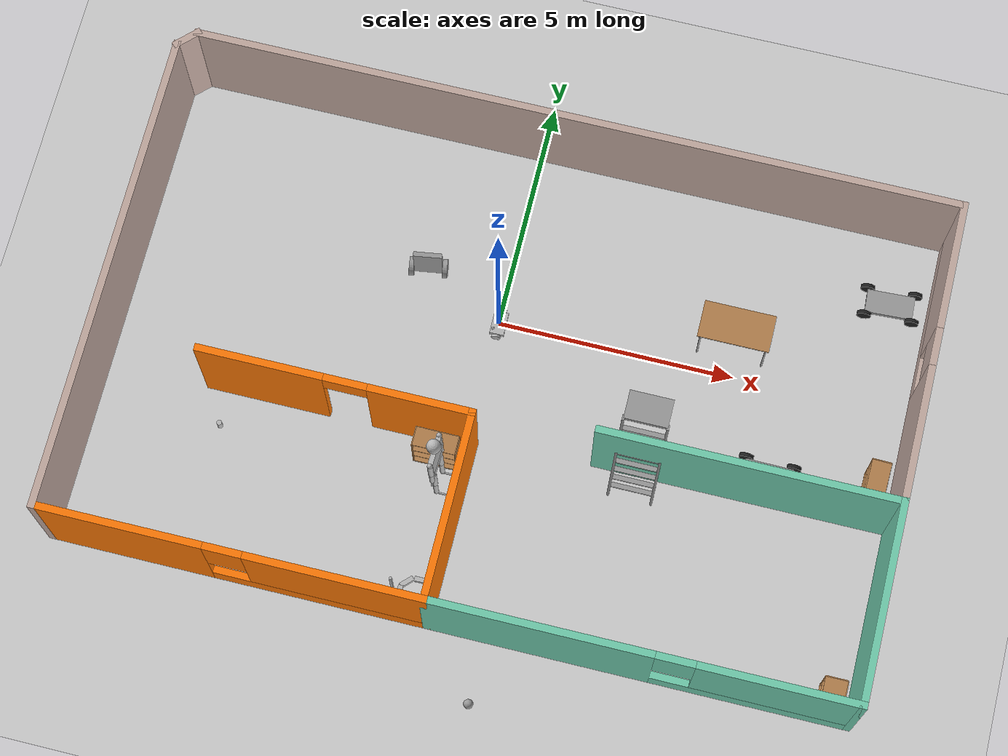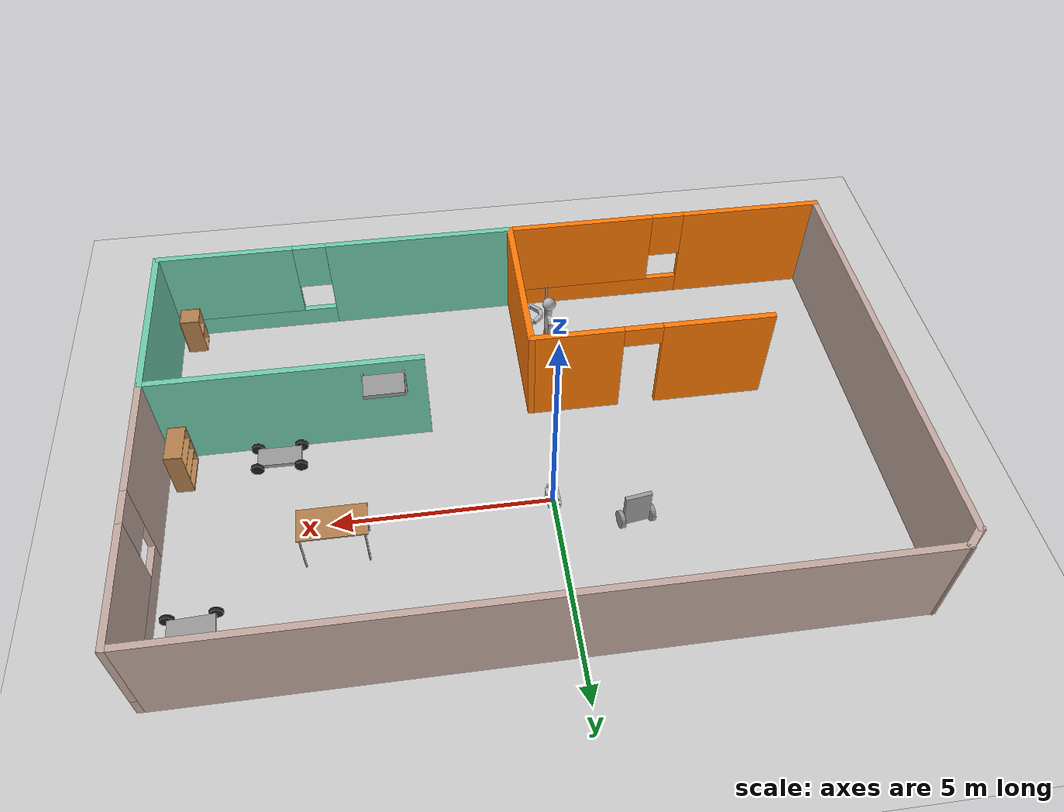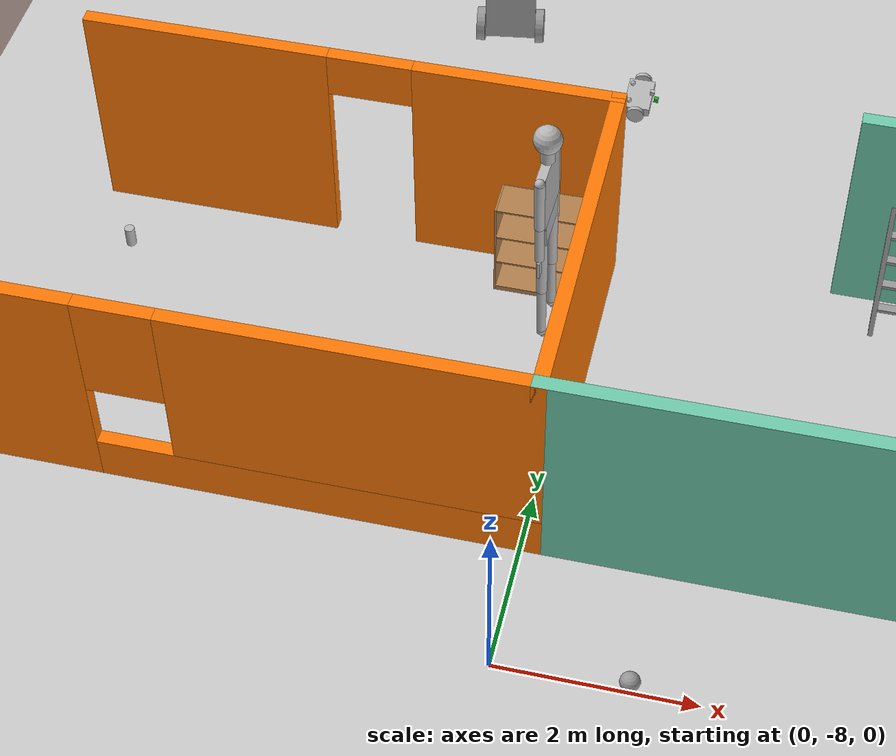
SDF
<sdf version="1.6">
 <world name="default">
  <plugin name="welcome_message" filename="libwelcome_message.so"/>
  <light name="sun" type="directional">
   <pose>0 0 10 0 -0 0</pose>
   <diffuse>0.8 0.8 0.8 1</diffuse>
   <specular>0.1 0.1 0.1 1</specular>
   <attenuation>
    <range>1000</range>
    <constant>0.9</constant>
    <linear>0.01</linear>
    <quadratic>0.001</quadratic>
   </attenuation>
   <direction>-0.5 0.5 -1</direction>
  </light>
  <model name="ground_plane">
   <static>1</static>
   <link name="link">
    <collision name="collision">
     <geometry><plane><normal>0 0 1</normal><size>100 100</size></plane></geometry>
     <surface><friction><ode><mu>100</mu><mu2>50</mu2></ode></friction></surface>
    </collision>
    <visual name="visual">
     <cast_shadows>0</cast_shadows>
     <geometry><plane><normal>0 0 1</normal><size>100 100</size></plane></geometry>
     <material>
      <script><uri>file://media/materials/scripts/gazebo.material</uri><name>Gazebo/Grey</name></script>
     </material>
    </visual>
   </link>
  </model>
  <gravity>0 0 -9.8</gravity>
  <magnetic_field>6e-06 2.3e-05 -4.2e-05</magnetic_field>
  <atmosphere type="adiabatic"/>
  <physics name="default_physics" default="0" type="ode">
   <max_step_size>0.001</max_step_size>
   <real_time_factor>1</real_time_factor>
   <real_time_update_rate>1000</real_time_update_rate>
  </physics>
  <scene><ambient>0.4 0.4 0.4 1</ambient><background>0.7 0.7 0.7 1</background><shadows>1</shadows></scene>
  <spherical_coordinates>
   <surface_model>EARTH_WGS84</surface_model>
   <latitude_deg>0</latitude_deg>
   <longitude_deg>0</longitude_deg>
   <elevation>0</elevation>
   <heading_deg>0</heading_deg>
  </spherical_coordinates>
  <model name="project1_robot">
   <link name="link_0">
    <pose>-0.000665 0 0.199997 0 -0 0</pose>
    <inertial>
     <mass>1</mass>
     <inertia>
      <ixx>0.166667</ixx>
      <ixy>0</ixy>
      <ixz>0</ixz>
      <iyy>0.166667</iyy>
      <iyz>0</iyz>
      <izz>0.166667</izz>
     </inertia>
    </inertial>
    <visual name="visual">
     <geometry><box><size>0.6 0.1 0.9</size></box></geometry>
     <material>
      <lighting>1</lighting>
      <script><uri>file://media/materials/scripts/gazebo.material</uri><name>Gazebo/Grey</name></script>
      <shader type="pixel"><normal_map>__default__</normal_map></shader>
      <ambient>0.3 0.3 0.3 1</ambient>
      <diffuse>0.7 0.7 0.7 1</diffuse>
      <specular>0.01 0.01 0.01 1</specular>
      <emissive>0 0 0 1</emissive>
     </material>
    </visual>
    <collision name="collision">
     <geometry><box><size>0.6 0.1 1</size></box></geometry>
     <surface>
      <friction>
       <ode><mu>1</mu><mu2>1</mu2><fdir1>0 0 0</fdir1><slip1>0</slip1><slip2>0</slip2></ode>
       <torsional>
        <coefficient>1</coefficient>
        <patch_radius>0</patch_radius>
        <surface_radius>0</surface_radius>
        <use_patch_radius>1</use_patch_radius>
        <ode><slip>0</slip></ode>
       </torsional>
      </friction>
      <bounce><restitution_coefficient>0</restitution_coefficient><threshold>1e+06</threshold></bounce>
      <contact>
       <collide_without_contact>0</collide_without_contact>
       <collide_without_contact_bitmask>1</collide_without_contact_bitmask>
       <collide_bitmask>1</collide_bitmask>
       <ode>
        <soft_cfm>0</soft_cfm>
        <soft_erp>0.2</soft_erp>
        <kp>1e+13</kp>
        <kd>1</kd>
        <max_vel>0.01</max_vel>
        <min_depth>0</min_depth>
       </ode>
       <bullet>
        <split_impulse>1</split_impulse>
        <split_impulse_penetration_threshold>-0.01</split_impulse_penetration_threshold>
        <soft_cfm>0</soft_cfm>
        <soft_erp>0.2</soft_erp>
        <kp>1e+13</kp>
        <kd>1</kd>
       </bullet>
      </contact>
     </surface>
    </collision>
   </link>
   <link name="link_1">
    <pose>0.351352 -0 -0.099508 0 -0.01 0</pose>
    <inertial>
     <mass>1</mass>
     <inertia><ixx>0.145833</ixx><ixy>0</ixy><ixz>0</ixz><iyy>0.145833</iyy><iyz>0</iyz><izz>0.125</izz></inertia>
    </inertial>
    <visual name="visual">
     <pose>0 0 0 0 1.5707 0</pose>
     <geometry><cylinder><radius>0.2</radius><length>0.1</length></cylinder></geometry>
     <material>
      <lighting>1</lighting>
      <script><uri>file://media/materials/scripts/gazebo.material</uri><name>Gazebo/Grey</name></script>
      <shader type="pixel"><normal_map>__default__</normal_map></shader>
      <ambient>0.3 0.3 0.3 1</ambient>
      <diffuse>0.7 0.7 0.7 1</diffuse>
      <specular>0.01 0.01 0.01 1</specular>
      <emissive>0 0 0 1</emissive>
     </material>
    </visual>
    <collision name="collision">
     <pose>0 0 0 0 1.5707 0</pose>
     <geometry><cylinder><radius>0.2</radius><length>0.1</length></cylinder></geometry>
     <surface>
      <friction>
       <ode><mu>1</mu><mu2>1</mu2><fdir1>0 0 0</fdir1><slip1>0</slip1><slip2>0</slip2></ode>
       <torsional>
        <coefficient>1</coefficient>
        <patch_radius>0</patch_radius>
        <surface_radius>0</surface_radius>
        <use_patch_radius>1</use_patch_radius>
        <ode><slip>0</slip></ode>
       </torsional>
      </friction>
      <bounce><restitution_coefficient>0</restitution_coefficient><threshold>1e+06</threshold></bounce>
      <contact>
       <collide_without_contact>0</collide_without_contact>
       <collide_without_contact_bitmask>1</collide_without_contact_bitmask>
       <collide_bitmask>1</collide_bitmask>
       <ode>
        <soft_cfm>0</soft_cfm>
        <soft_erp>0.2</soft_erp>
        <kp>1e+13</kp>
        <kd>1</kd>
        <max_vel>0.01</max_vel>
        <min_depth>0</min_depth>
       </ode>
       <bullet>
        <split_impulse>1</split_impulse>
        <split_impulse_penetration_threshold>-0.01</split_impulse_penetration_threshold>
        <soft_cfm>0</soft_cfm>
        <soft_erp>0.2</soft_erp>
        <kp>1e+13</kp>
        <kd>1</kd>
       </bullet>
      </contact>
     </surface>
    </collision>
   </link>
   <link name="link_1_clone">
    <pose>-0.350684 0 -0.099999 0 -0 0</pose>
    <inertial>
     <mass>1</mass>
     <inertia><ixx>0.145833</ixx><ixy>0</ixy><ixz>0</ixz><iyy>0.145833</iyy><iyz>0</iyz><izz>0.125</izz></inertia>
    </inertial>
    <visual name="visual">
     <pose>0 0 0 0 1.5707 0</pose>
     <geometry><cylinder><radius>0.2</radius><length>0.1</length></cylinder></geometry>
     <material>
      <lighting>1</lighting>
      <script><uri>file://media/materials/scripts/gazebo.material</uri><name>Gazebo/Grey</name></script>
      <shader type="pixel"><normal_map>__default__</normal_map></shader>
      <ambient>0.3 0.3 0.3 1</ambient>
      <diffuse>0.7 0.7 0.7 1</diffuse>
      <specular>0.01 0.01 0.01 1</specular>
      <emissive>0 0 0 1</emissive>
     </material>
    </visual>
    <collision name="collision">
     <pose>0 0 0 0 1.5707 0</pose>
     <geometry><cylinder><radius>0.2</radius><length>0.1</length></cylinder></geometry>
     <surface>
      <friction>
       <ode><mu>1</mu><mu2>1</mu2><fdir1>0 0 0</fdir1><slip1>0</slip1><slip2>0</slip2></ode>
       <torsional>
        <coefficient>1</coefficient>
        <patch_radius>0</patch_radius>
        <surface_radius>0</surface_radius>
        <use_patch_radius>1</use_patch_radius>
        <ode><slip>0</slip></ode>
       </torsional>
      </friction>
      <bounce><restitution_coefficient>0</restitution_coefficient><threshold>1e+06</threshold></bounce>
      <contact>
       <collide_without_contact>0</collide_without_contact>
       <collide_without_contact_bitmask>1</collide_without_contact_bitmask>
       <collide_bitmask>1</collide_bitmask>
       <ode>
        <soft_cfm>0</soft_cfm>
        <soft_erp>0.2</soft_erp>
        <kp>1e+13</kp>
        <kd>1</kd>
        <max_vel>0.01</max_vel>
        <min_depth>0</min_depth>
       </ode>
       <bullet>
        <split_impulse>1</split_impulse>
        <split_impulse_penetration_threshold>-0.01</split_impulse_penetration_threshold>
        <soft_cfm>0</soft_cfm>
        <soft_erp>0.2</soft_erp>
        <kp>1e+13</kp>
        <kd>1</kd>
       </bullet>
      </contact>
     </surface>
    </collision>
   </link>
   <joint name="link_0_JOINT_1" type="revolute2">
    <parent>link_0</parent>
    <child>link_1</child>
    <axis>
     <xyz>1 0 0</xyz>
     <use_parent_model_frame>0</use_parent_model_frame>
     <limit>
      <lower>-1.79769e+308</lower>
      <upper>1.79769e+308</upper>
      <effort>-1</effort>
      <velocity>-1</velocity>
     </limit>
     <dynamics>
      <spring_reference>0</spring_reference>
      <spring_stiffness>0</spring_stiffness>
      <damping>0</damping>
     </dynamics>
    </axis>
    <axis2>
     <xyz>0 1 0</xyz>
     <use_parent_model_frame>0</use_parent_model_frame>
     <dynamics>
      <spring_reference>0</spring_reference>
      <spring_stiffness>0</spring_stiffness>
      <damping>0</damping>
     </dynamics>
     <limit>
      <lower>-1.79769e+308</lower>
      <upper>1.79769e+308</upper>
      <effort>-1</effort>
      <velocity>-1</velocity>
     </limit>
    </axis2>
    <physics>
     <ode><limit><cfm>0</cfm><erp>0.2</erp></limit><suspension><cfm>0</cfm><erp>0.2</erp></suspension></ode>
    </physics>
   </joint>
   <joint name="link_1_clone_JOINT_2" type="revolute2">
    <parent>link_0</parent>
    <child>link_1_clone</child>
    <axis>
     <xyz>1 0 0</xyz>
     <use_parent_model_frame>0</use_parent_model_frame>
     <limit>
      <lower>-1.79769e+308</lower>
      <upper>1.79769e+308</upper>
      <effort>-1</effort>
      <velocity>-1</velocity>
     </limit>
     <dynamics>
      <spring_reference>0</spring_reference>
      <spring_stiffness>0</spring_stiffness>
      <damping>0</damping>
     </dynamics>
    </axis>
    <axis2>
     <xyz>0 1 0</xyz>
     <use_parent_model_frame>0</use_parent_model_frame>
     <dynamics>
      <spring_reference>0</spring_reference>
      <spring_stiffness>0</spring_stiffness>
      <damping>0</damping>
     </dynamics>
     <limit>
      <lower>-1.79769e+308</lower>
      <upper>1.79769e+308</upper>
      <effort>-1</effort>
      <velocity>-1</velocity>
     </limit>
    </axis2>
    <physics>
     <ode><limit><cfm>0</cfm><erp>0.2</erp></limit><suspension><cfm>0</cfm><erp>0.2</erp></suspension></ode>
    </physics>
   </joint>
   <static>0</static>
   <pose>-1.72829 0.801476 0.300027 -4e-06 -7.9e-05 0.148534</pose>
  </model>
  <model name="table">
   <static>1</static>
   <link name="link">
    <collision name="surface">
     <pose>0 0 1 0 -0 0</pose>
     <geometry><box><size>1.5 0.8 0.03</size></box></geometry>
     <surface><friction><ode><mu>0.6</mu><mu2>0.6</mu2></ode></friction></surface>
    </collision>
    <visual name="visual1">
     <pose>0 0 1 0 -0 0</pose>
     <geometry><box><size>1.5 0.8 0.03</size></box></geometry>
     <material>
      <script><uri>file://media/materials/scripts/gazebo.material</uri><name>Gazebo/Wood</name></script>
     </material>
    </visual>
    <collision name="front_left_leg">
     <pose>0.68 0.38 0.5 0 -0 0</pose>
     <geometry><cylinder><radius>0.02</radius><length>1</length></cylinder></geometry>
    </collision>
    <visual name="front_left_leg">
     <pose>0.68 0.38 0.5 0 -0 0</pose>
     <geometry><cylinder><radius>0.02</radius><length>1</length></cylinder></geometry>
     <material>
      <script><uri>file://media/materials/scripts/gazebo.material</uri><name>Gazebo/Grey</name></script>
     </material>
    </visual>
    <collision name="front_right_leg">
     <pose>0.68 -0.38 0.5 0 -0 0</pose>
     <geometry><cylinder><radius>0.02</radius><length>1</length></cylinder></geometry>
    </collision>
    <visual name="front_right_leg">
     <pose>0.68 -0.38 0.5 0 -0 0</pose>
     <geometry><cylinder><radius>0.02</radius><length>1</length></cylinder></geometry>
     <material>
      <script><uri>file://media/materials/scripts/gazebo.material</uri><name>Gazebo/Grey</name></script>
     </material>
    </visual>
    <collision name="back_right_leg">
     <pose>-0.68 -0.38 0.5 0 -0 0</pose>
     <geometry><cylinder><radius>0.02</radius><length>1</length></cylinder></geometry>
    </collision>
    <visual name="back_right_leg">
     <pose>-0.68 -0.38 0.5 0 -0 0</pose>
     <geometry><cylinder><radius>0.02</radius><length>1</length></cylinder></geometry>
     <material>
      <script><uri>file://media/materials/scripts/gazebo.material</uri><name>Gazebo/Grey</name></script>
     </material>
    </visual>
    <collision name="back_left_leg">
     <pose>-0.68 0.38 0.5 0 -0 0</pose>
     <geometry><cylinder><radius>0.02</radius><length>1</length></cylinder></geometry>
    </collision>
    <visual name="back_left_leg">
     <pose>-0.68 0.38 0.5 0 -0 0</pose>
     <geometry><cylinder><radius>0.02</radius><length>1</length></cylinder></geometry>
     <material>
      <script><uri>file://media/materials/scripts/gazebo.material</uri><name>Gazebo/Grey</name></script>
     </material>
    </visual>
   </link>
   <pose>4.82921 0.731806 0.12916 0 -0 0</pose>
  </model>
  <model name="beer">
   <link name="link">
    <pose>0 0 0.115 0 -0 0</pose>
    <inertial>
     <mass>0.39</mass>
     <inertia><ixx>0.00058</ixx><ixy>0</ixy><ixz>0</ixz><iyy>0.00058</iyy><iyz>0</iyz><izz>0.00019</izz></inertia>
    </inertial>
    <collision name="collision">
     <geometry><cylinder><radius>0.055</radius><length>0.23</length></cylinder></geometry>
    </collision>
    <visual name="visual">
     <geometry><cylinder><radius>0.055</radius><length>0.23</length></cylinder></geometry>
     <material>
      <script>
       <uri>model://beer/materials/scripts</uri>
       <uri>model://beer/materials/textures</uri>
       <name>Beer/Diffuse</name>
      </script>
     </material>
    </visual>
   </link>
   <pose>-5.06977 -3.53298 -7e-06 -1e-06 0 -6.6e-05</pose>
  </model>
  <model name="house">
   <pose>0.48898 -1.33717 0 0 -0 0</pose>
   <link name="Wall_0">
    <collision name="Wall_0_Collision">
     <geometry><box><size>10.25 0.15 2.5</size></box></geometry>
     <pose>0 0 1.25 0 -0 0</pose>
    </collision>
    <visual name="Wall_0_Visual">
     <pose>0 0 1.25 0 -0 0</pose>
     <geometry><box><size>10.25 0.15 2.5</size></box></geometry>
     <material>
      <script><uri>file://media/materials/scripts/gazebo.material</uri><name>Gazebo/Grey</name></script>
      <ambient>0.760784 0.662745 0.627451 1</ambient>
     </material>
     <meta><layer>0</layer></meta>
    </visual>
    <pose>-8.20947 -0.190533 0 0 0 -1.5708</pose>
   </link>
   <link name="Wall_10">
    <pose>8.24053 2.03447 0 0 -0 1.5708</pose>
    <visual name="Wall_10_Visual_0">
     <pose>-1.78129 0 1.25 0 -0 0</pose>
     <geometry><box><size>2.93743 0.15 2.5</size></box></geometry>
     <material>
      <script><uri>file://media/materials/scripts/gazebo.material</uri><name>Gazebo/Grey</name></script>
      <ambient>0.760784 0.662745 0.627451 1</ambient>
     </material>
     <meta><layer>0</layer></meta>
    </visual>
    <collision name="Wall_10_Collision_0">
     <geometry><box><size>2.93743 0.15 2.5</size></box></geometry>
     <pose>-1.78129 0 1.25 0 -0 0</pose>
    </collision>
    <visual name="Wall_10_Visual_1">
     <pose>1.46871 0 0.25 0 -0 0</pose>
     <geometry><box><size>3.56257 0.15 0.5</size></box></geometry>
     <material>
      <script><uri>file://media/materials/scripts/gazebo.material</uri><name>Gazebo/Grey</name></script>
      <ambient>0.760784 0.662745 0.627451 1</ambient>
     </material>
     <meta><layer>0</layer></meta>
    </visual>
    <collision name="Wall_10_Collision_1">
     <geometry><box><size>3.56257 0.15 0.5</size></box></geometry>
     <pose>1.46871 0 0.25 0 -0 0</pose>
    </collision>
    <visual name="Wall_10_Visual_2">
     <pose>1.86871 0 1.5 0 -0 0</pose>
     <geometry><box><size>2.76258 0.15 2</size></box></geometry>
     <material>
      <script><uri>file://media/materials/scripts/gazebo.material</uri><name>Gazebo/Grey</name></script>
      <ambient>0.760784 0.662745 0.627451 1</ambient>
     </material>
     <meta><layer>0</layer></meta>
    </visual>
    <collision name="Wall_10_Collision_2">
     <geometry><box><size>2.76258 0.15 2</size></box></geometry>
     <pose>1.86871 0 1.5 0 -0 0</pose>
    </collision>
    <visual name="Wall_10_Visual_3">
     <pose>0.087425 0 1.9 0 -0 0</pose>
     <geometry><box><size>0.8 0.15 1.2</size></box></geometry>
     <material>
      <script><uri>file://media/materials/scripts/gazebo.material</uri><name>Gazebo/Grey</name></script>
      <ambient>0.760784 0.662745 0.627451 1</ambient>
     </material>
     <meta><layer>0</layer></meta>
    </visual>
    <collision name="Wall_10_Collision_3">
     <geometry><box><size>0.8 0.15 1.2</size></box></geometry>
     <pose>0.087425 0 1.9 0 -0 0</pose>
    </collision>
   </link>
   <link name="Wall_11">
    <collision name="Wall_11_Collision">
     <geometry><box><size>16.25 0.15 2.5</size></box></geometry>
     <pose>0 0 1.25 0 -0 0</pose>
    </collision>
    <visual name="Wall_11_Visual">
     <pose>0 0 1.25 0 -0 0</pose>
     <geometry><box><size>16.25 0.15 2.5</size></box></geometry>
     <material>
      <script><uri>file://media/materials/scripts/gazebo.material</uri><name>Gazebo/Grey</name></script>
      <ambient>0.760784 0.662745 0.627451 1</ambient>
     </material>
     <meta><layer>0</layer></meta>
    </visual>
    <pose>0.190533 5.20947 0 0 -0 3.14159</pose>
   </link>
   <link name="Wall_12">
    <collision name="Wall_12_Collision">
     <geometry><box><size>0.644975 0.15 2.5</size></box></geometry>
     <pose>0 0 1.25 0 -0 0</pose>
    </collision>
    <visual name="Wall_12_Visual">
     <pose>0 0 1.25 0 -0 0</pose>
     <geometry><box><size>0.644975 0.15 2.5</size></box></geometry>
     <material>
      <script><uri>file://media/materials/scripts/gazebo.material</uri><name>Gazebo/Grey</name></script>
      <ambient>0.760784 0.662745 0.627451 1</ambient>
     </material>
     <meta><layer>0</layer></meta>
    </visual>
    <pose>-8.03447 5.03447 0 0 0 -2.35619</pose>
   </link>
   <link name="Wall_2">
    <pose>-4.28447 -5.24053 0 0 -0 0</pose>
    <visual name="Wall_2_Visual_0">
     <pose>-2.2462 0 1.25 0 -0 0</pose>
     <geometry><box><size>3.5076 0.15 2.5</size></box></geometry>
     <material>
      <script><uri>file://media/materials/scripts/gazebo.material</uri><name>Gazebo/Grey</name></script>
      <ambient>0.996078 0.47451 0.0196078 1</ambient>
     </material>
     <meta><layer>0</layer></meta>
    </visual>
    <collision name="Wall_2_Collision_0">
     <geometry><box><size>3.5076 0.15 2.5</size></box></geometry>
     <pose>-2.2462 0 1.25 0 -0 0</pose>
    </collision>
    <visual name="Wall_2_Visual_1">
     <pose>1.7538 0 0.25 0 -0 0</pose>
     <geometry><box><size>4.4924 0.15 0.5</size></box></geometry>
     <material>
      <script><uri>file://media/materials/scripts/gazebo.material</uri><name>Gazebo/Grey</name></script>
      <ambient>0.996078 0.47451 0.0196078 1</ambient>
     </material>
     <meta><layer>0</layer></meta>
    </visual>
    <collision name="Wall_2_Collision_1">
     <geometry><box><size>4.4924 0.15 0.5</size></box></geometry>
     <pose>1.7538 0 0.25 0 -0 0</pose>
    </collision>
    <visual name="Wall_2_Visual_2">
     <pose>2.1538 0 1.5 0 -0 0</pose>
     <geometry><box><size>3.69239 0.15 2</size></box></geometry>
     <material>
      <script><uri>file://media/materials/scripts/gazebo.material</uri><name>Gazebo/Grey</name></script>
      <ambient>0.996078 0.47451 0.0196078 1</ambient>
     </material>
     <meta><layer>0</layer></meta>
    </visual>
    <collision name="Wall_2_Collision_2">
     <geometry><box><size>3.69239 0.15 2</size></box></geometry>
     <pose>2.1538 0 1.5 0 -0 0</pose>
    </collision>
    <visual name="Wall_2_Visual_3">
     <pose>-0.092395 0 1.9 0 -0 0</pose>
     <geometry><box><size>0.8 0.15 1.2</size></box></geometry>
     <material>
      <script><uri>file://media/materials/scripts/gazebo.material</uri><name>Gazebo/Grey</name></script>
      <ambient>0.996078 0.47451 0.0196078 1</ambient>
     </material>
     <meta><layer>0</layer></meta>
    </visual>
    <collision name="Wall_2_Collision_3">
     <geometry><box><size>0.8 0.15 1.2</size></box></geometry>
     <pose>-0.092395 0 1.9 0 -0 0</pose>
    </collision>
   </link>
   <link name="Wall_3">
    <collision name="Wall_3_Collision">
     <geometry><box><size>4 0.15 2.5</size></box></geometry>
     <pose>0 0 1.25 0 -0 0</pose>
    </collision>
    <visual name="Wall_3_Visual">
     <pose>0 0 1.25 0 -0 0</pose>
     <geometry><box><size>4 0.15 2.5</size></box></geometry>
     <material>
      <script><uri>file://media/materials/scripts/gazebo.material</uri><name>Gazebo/Grey</name></script>
      <ambient>0.996078 0.47451 0.0196078 1</ambient>
     </material>
     <meta><layer>0</layer></meta>
    </visual>
    <pose>-0.359467 -3.31553 0 0 -0 1.5708</pose>
   </link>
   <link name="Wall_4">
    <pose>-3.15947 -1.39053 0 0 -0 3.14159</pose>
    <visual name="Wall_4_Visual_0">
     <pose>-1.76861 0 1.25 0 -0 0</pose>
     <geometry><box><size>2.21277 0.15 2.5</size></box></geometry>
     <material>
      <script><uri>file://media/materials/scripts/gazebo.material</uri><name>Gazebo/Grey</name></script>
      <ambient>0.996078 0.47451 0.0196078 1</ambient>
     </material>
     <meta><layer>0</layer></meta>
    </visual>
    <collision name="Wall_4_Collision_0">
     <geometry><box><size>2.21277 0.15 2.5</size></box></geometry>
     <pose>-1.76861 0 1.25 0 -0 0</pose>
    </collision>
    <visual name="Wall_4_Visual_1">
     <pose>1.55639 0 1.25 0 -0 0</pose>
     <geometry><box><size>2.63723 0.15 2.5</size></box></geometry>
     <material>
      <script><uri>file://media/materials/scripts/gazebo.material</uri><name>Gazebo/Grey</name></script>
      <ambient>0.996078 0.47451 0.0196078 1</ambient>
     </material>
     <meta><layer>0</layer></meta>
    </visual>
    <collision name="Wall_4_Collision_1">
     <geometry><box><size>2.63723 0.15 2.5</size></box></geometry>
     <pose>1.55639 0 1.25 0 -0 0</pose>
    </collision>
    <visual name="Wall_4_Visual_2">
     <pose>-0.212228 0 2.25 0 -0 0</pose>
     <geometry><box><size>0.9 0.15 0.5</size></box></geometry>
     <material>
      <script><uri>file://media/materials/scripts/gazebo.material</uri><name>Gazebo/Grey</name></script>
      <ambient>0.996078 0.47451 0.0196078 1</ambient>
     </material>
     <meta><layer>0</layer></meta>
    </visual>
    <collision name="Wall_4_Collision_2">
     <geometry><box><size>0.9 0.15 0.5</size></box></geometry>
     <pose>-0.212228 0 2.25 0 -0 0</pose>
    </collision>
   </link>
   <link name="Wall_6">
    <pose>3.94053 -5.24053 0 0 -0 0</pose>
    <visual name="Wall_6_Visual_0">
     <pose>-2.05962 0 1.25 0 -0 0</pose>
     <geometry><box><size>4.63077 0.15 2.5</size></box></geometry>
     <material>
      <script><uri>file://media/materials/scripts/gazebo.material</uri><name>Gazebo/Grey</name></script>
      <ambient>0.435294 0.796078 0.67451 1</ambient>
     </material>
     <meta><layer>0</layer></meta>
    </visual>
    <collision name="Wall_6_Collision_0">
     <geometry><box><size>4.63077 0.15 2.5</size></box></geometry>
     <pose>-2.05962 0 1.25 0 -0 0</pose>
    </collision>
    <visual name="Wall_6_Visual_1">
     <pose>2.31538 0 0.25 0 -0 0</pose>
     <geometry><box><size>4.11923 0.15 0.5</size></box></geometry>
     <material>
      <script><uri>file://media/materials/scripts/gazebo.material</uri><name>Gazebo/Grey</name></script>
      <ambient>0.435294 0.796078 0.67451 1</ambient>
     </material>
     <meta><layer>0</layer></meta>
    </visual>
    <collision name="Wall_6_Collision_1">
     <geometry><box><size>4.11923 0.15 0.5</size></box></geometry>
     <pose>2.31538 0 0.25 0 -0 0</pose>
    </collision>
    <visual name="Wall_6_Visual_2">
     <pose>2.71538 0 1.5 0 -0 0</pose>
     <geometry><box><size>3.31923 0.15 2</size></box></geometry>
     <material>
      <script><uri>file://media/materials/scripts/gazebo.material</uri><name>Gazebo/Grey</name></script>
      <ambient>0.435294 0.796078 0.67451 1</ambient>
     </material>
     <meta><layer>0</layer></meta>
    </visual>
    <collision name="Wall_6_Collision_2">
     <geometry><box><size>3.31923 0.15 2</size></box></geometry>
     <pose>2.71538 0 1.5 0 -0 0</pose>
    </collision>
    <visual name="Wall_6_Visual_3">
     <pose>0.655767 0 1.9 0 -0 0</pose>
     <geometry><box><size>0.8 0.15 1.2</size></box></geometry>
     <material>
      <script><uri>file://media/materials/scripts/gazebo.material</uri><name>Gazebo/Grey</name></script>
      <ambient>0.435294 0.796078 0.67451 1</ambient>
     </material>
     <meta><layer>0</layer></meta>
    </visual>
    <collision name="Wall_6_Collision_3">
     <geometry><box><size>0.8 0.15 1.2</size></box></geometry>
     <pose>0.655767 0 1.9 0 -0 0</pose>
    </collision>
   </link>
   <link name="Wall_7">
    <collision name="Wall_7_Collision">
     <geometry><box><size>4.25 0.15 2.5</size></box></geometry>
     <pose>0 0 1.25 0 -0 0</pose>
    </collision>
    <visual name="Wall_7_Visual">
     <pose>0 0 1.25 0 -0 0</pose>
     <geometry><box><size>4.25 0.15 2.5</size></box></geometry>
     <material>
      <script><uri>file://media/materials/scripts/gazebo.material</uri><name>Gazebo/Grey</name></script>
      <ambient>0.435294 0.796078 0.67451 1</ambient>
     </material>
     <meta><layer>0</layer></meta>
    </visual>
    <pose>8.24053 -3.19053 0 0 -0 1.5708</pose>
   </link>
   <link name="Wall_8">
    <collision name="Wall_8_Collision">
     <geometry><box><size>6.25 0.15 2.5</size></box></geometry>
     <pose>0 0 1.25 0 -0 0</pose>
    </collision>
    <visual name="Wall_8_Visual">
     <pose>0 0 1.25 0 -0 0</pose>
     <geometry><box><size>6.25 0.15 2.5</size></box></geometry>
     <material>
      <script><uri>file://media/materials/scripts/gazebo.material</uri><name>Gazebo/Grey</name></script>
      <ambient>0.435294 0.796078 0.67451 1</ambient>
     </material>
     <meta><layer>0</layer></meta>
    </visual>
    <pose>5.19053 -1.14053 0 0 -0 3.14159</pose>
   </link>
   <static>1</static>
  </model>
  <model name="unit_sphere">
   <link name="link">
    <inertial>
     <mass>1</mass>
     <inertia><ixx>0.1</ixx><ixy>0</ixy><ixz>0</ixz><iyy>0.1</iyy><iyz>0</iyz><izz>0.1</izz></inertia>
    </inertial>
    <visual name="visual">
     <geometry><sphere><radius>0.1</radius></sphere></geometry>
     <material>
      <script><name>Gazebo/Grey</name><uri>file://media/materials/scripts/gazebo.material</uri></script>
      <shader type="pixel"><normal_map>__default__</normal_map></shader>
      <ambient>1 1 1 1</ambient>
      <diffuse>1 1 1 1</diffuse>
      <specular>1 1 1 1</specular>
      <emissive>1 1 1 1</emissive>
     </material>
    </visual>
    <collision name="collision">
     <geometry><sphere><radius>0.1</radius></sphere></geometry>
     <surface>
      <friction>
       <ode><mu>1</mu><mu2>1</mu2><fdir1>0 0 0</fdir1><slip1>0</slip1><slip2>0</slip2></ode>
       <torsional>
        <coefficient>1</coefficient>
        <patch_radius>0</patch_radius>
        <surface_radius>0</surface_radius>
        <use_patch_radius>1</use_patch_radius>
        <ode><slip>0</slip></ode>
       </torsional>
      </friction>
      <bounce><restitution_coefficient>0</restitution_coefficient><threshold>1e+06</threshold></bounce>
      <contact>
       <collide_without_contact>0</collide_without_contact>
       <collide_without_contact_bitmask>1</collide_without_contact_bitmask>
       <collide_bitmask>1</collide_bitmask>
       <ode>
        <soft_cfm>0</soft_cfm>
        <soft_erp>0.2</soft_erp>
        <kp>1e+13</kp>
        <kd>1</kd>
        <max_vel>0.01</max_vel>
        <min_depth>0</min_depth>
       </ode>
       <bullet>
        <split_impulse>1</split_impulse>
        <split_impulse_penetration_threshold>-0.01</split_impulse_penetration_threshold>
        <soft_cfm>0</soft_cfm>
        <soft_erp>0.2</soft_erp>
        <kp>1e+13</kp>
        <kd>1</kd>
       </bullet>
      </contact>
     </surface>
    </collision>
   </link>
   <static>0</static>
   <pose>1.31942 -7.94245 0.1 0 -0 0</pose>
  </model>
  <model name="my_robot">
   <link name="robot_footprint">
    <inertial>
     <pose>0.001325 0 0 0 -0 0</pose>
     <mass>15.1</mass>
     <inertia>
      <ixx>0.100002</ixx>
      <ixy>0</ixy>
      <ixz>-1.48675e-07</ixz>
      <iyy>0.103976</iyy>
      <iyz>0</iyz>
      <izz>0.103976</izz>
     </inertia>
    </inertial>
    <collision name="robot_footprint_fixed_joint_lump__collision_collision">
     <geometry><box><size>0.3 0.5 0.1</size></box></geometry>
    </collision>
    <collision name="robot_footprint_fixed_joint_lump__back_caster_collision_collision_1">
     <pose>-0.1 0 -0.05 0 -0 0</pose>
     <geometry><sphere><radius>0.0499</radius></sphere></geometry>
    </collision>
    <collision name="robot_footprint_fixed_joint_lump__front_caster_collision_collision_2">
     <pose>0.1 0 -0.05 0 -0 0</pose>
     <geometry><sphere><radius>0.0499</radius></sphere></geometry>
    </collision>
    <collision name="robot_footprint_fixed_joint_lump__left_eye_collision_collision_3">
     <pose>-0.1 0.15 0.07 0 -0 0</pose>
     <geometry><sphere><radius>0.03</radius></sphere></geometry>
    </collision>
    <collision name="robot_footprint_fixed_joint_lump__right_eye_collision_collision_4">
     <pose>-0.1 -0.15 0.07 0 -0 0</pose>
     <geometry><sphere><radius>0.03</radius></sphere></geometry>
    </collision>
    <collision name="robot_footprint_fixed_joint_lump__camera_collision_collision_5">
     <pose>0.2 0 0 0 -0 0</pose>
     <geometry><box><size>0.05 0.05 0.05</size></box></geometry>
    </collision>
    <collision name="robot_footprint_fixed_joint_lump__hokuyo_collision_collision_6">
     <pose>0.15 0 0.1 0 -0 0</pose>
     <geometry>
      <mesh><scale>1 1 1</scale><uri>/home/workspace/catkin_ws/src/my_robot/meshes/hokuyo.dae</uri></mesh>
     </geometry>
    </collision>
    <visual name="robot_footprint_fixed_joint_lump__chassis_visual_visual">
     <geometry><box><size>0.3 0.5 0.1</size></box></geometry>
    </visual>
    <visual name="robot_footprint_fixed_joint_lump__back_caster_visual_visual_1">
     <pose>-0.1 0 -0.05 0 -0 0</pose>
     <geometry><sphere><radius>0.05</radius></sphere></geometry>
    </visual>
    <visual name="robot_footprint_fixed_joint_lump__front_caster_visual_visual_2">
     <pose>0.1 0 -0.05 0 -0 0</pose>
     <geometry><sphere><radius>0.05</radius></sphere></geometry>
    </visual>
    <visual name="robot_footprint_fixed_joint_lump__left_eye_visual_visual_3">
     <pose>-0.1 0.15 0.07 0 -0 0</pose>
     <geometry><sphere><radius>0.03</radius></sphere></geometry>
    </visual>
    <visual name="robot_footprint_fixed_joint_lump__right_eye_visual_visual_4">
     <pose>-0.1 -0.15 0.07 0 -0 0</pose>
     <geometry><sphere><radius>0.03</radius></sphere></geometry>
    </visual>
    <visual name="robot_footprint_fixed_joint_lump__camera_visual_visual_5">
     <pose>0.2 0 0 0 -0 0</pose>
     <geometry><box><size>0.05 0.05 0.05</size></box></geometry>
     <material>
      <script><name>Gazebo/Green</name><uri>file://media/materials/scripts/gazebo.material</uri></script>
     </material>
    </visual>
    <visual name="robot_footprint_fixed_joint_lump__hokuyo_visual_visual_6">
     <pose>0.15 0 0.1 0 -0 0</pose>
     <geometry><box><size>0.05 0.05 0.05</size></box></geometry>
     <material><script><uri>__default__</uri><name>__default__</name></script></material>
    </visual>
    <sensor name="camera1" type="depth">
     <always_on>1</always_on>
     <update_rate>20</update_rate>
     <visualize>1</visualize>
     <camera name="__default__">
      <horizontal_fov>1.047</horizontal_fov>
      <image><width>640</width><height>480</height><format>R8G8B8</format></image>
      <depth_camera><output>depths</output></depth_camera>
      <clip><near>0.1</near><far>20</far></clip>
     </camera>
     <plugin name="camera_controller" filename="libgazebo_ros_openni_kinect.so">
      <alwaysOn>true</alwaysOn>
      <updateRate>10.0</updateRate>
      <cameraName>camera</cameraName>
      <frameName>camera_link_optical</frameName>
      <imageTopicName>rgb/image_raw</imageTopicName>
      <depthImageTopicName>depth/image_raw</depthImageTopicName>
      <pointCloudTopicName>depth/points</pointCloudTopicName>
      <cameraInfoTopicName>rgb/camera_info</cameraInfoTopicName>
      <depthImageCameraInfoTopicName>depth/camera_info</depthImageCameraInfoTopicName>
      <pointCloudCutoff>0.4</pointCloudCutoff>
      <hackBaseline>0.07</hackBaseline>
      <distortionK1>0.0</distortionK1>
      <distortionK2>0.0</distortionK2>
      <distortionK3>0.0</distortionK3>
      <distortionT1>0.0</distortionT1>
      <distortionT2>0.0</distortionT2>
      <CxPrime>0.0</CxPrime>
      <Cx>0.0</Cx>
      <Cy>0.0</Cy>
      <focalLength>0.0</focalLength>
      <robotNamespace>/</robotNamespace>
     </plugin>
     <pose>0.2 0 0 0 -0 0</pose>
    </sensor>
    <sensor name="head_hokuyo_sensor" type="ray">
     <visualize>0</visualize>
     <update_rate>40</update_rate>
     <ray>
      <scan>
       <horizontal>
        <samples>720</samples>
        <resolution>1</resolution>
        <min_angle>-1.5708</min_angle>
        <max_angle>1.5708</max_angle>
       </horizontal>
       <vertical><samples>1</samples><min_angle>0</min_angle><max_angle>0</max_angle></vertical>
      </scan>
      <range><min>0.1</min><max>30</max><resolution>0.01</resolution></range>
      <noise><type>gaussian</type><mean>0</mean><stddev>0.01</stddev></noise>
     </ray>
     <plugin name="gazebo_ros_head_hokuyo_controller" filename="libgazebo_ros_laser.so">
      <topicName>/scan</topicName>
      <frameName>hokuyo</frameName>
      <robotNamespace>/</robotNamespace>
     </plugin>
     <pose>0.15 0 0.1 0 -0 0</pose>
    </sensor>
   </link>
   <link name="left_wheel">
    <pose>0 0.3 0 0 -0 0</pose>
    <inertial>
     <pose>0 0 0 -0 1.5707 1.5707</pose>
     <mass>5</mass>
     <inertia><ixx>0.1</ixx><ixy>0</ixy><ixz>0</ixz><iyy>0.1</iyy><iyz>0</iyz><izz>0.1</izz></inertia>
    </inertial>
    <collision name="left_wheel_collision_collision">
     <pose>0 0 0 3.14159 1.57079 -1.57089</pose>
     <geometry><cylinder><length>0.05</length><radius>0.1</radius></cylinder></geometry>
    </collision>
    <visual name="left_wheel_visual_visual">
     <pose>0 0 0 3.14159 1.57079 -1.57089</pose>
     <geometry><cylinder><length>0.05</length><radius>0.1</radius></cylinder></geometry>
    </visual>
   </link>
   <joint name="left_wheel_hinge" type="revolute">
    <child>left_wheel</child>
    <parent>robot_footprint</parent>
    <axis>
     <xyz>0 1 0</xyz>
     <limit><lower>-1e+16</lower><upper>1e+16</upper></limit>
     <dynamics>
      <damping>1</damping>
      <friction>1</friction>
      <spring_reference>0</spring_reference>
      <spring_stiffness>0</spring_stiffness>
     </dynamics>
     <use_parent_model_frame>1</use_parent_model_frame>
    </axis>
   </joint>
   <link name="right_wheel">
    <pose>0 -0.3 0 0 -0 0</pose>
    <inertial>
     <pose>0 0 0 -0 1.5707 1.5707</pose>
     <mass>5</mass>
     <inertia><ixx>0.1</ixx><ixy>0</ixy><ixz>0</ixz><iyy>0.1</iyy><iyz>0</iyz><izz>0.1</izz></inertia>
    </inertial>
    <collision name="right_wheel_collision_collision">
     <pose>0 0 0 3.14159 1.57079 -1.57089</pose>
     <geometry><cylinder><length>0.05</length><radius>0.1</radius></cylinder></geometry>
    </collision>
    <visual name="right_wheel_visual_visual">
     <pose>0 0 0 3.14159 1.57079 -1.57089</pose>
     <geometry><cylinder><length>0.05</length><radius>0.1</radius></cylinder></geometry>
    </visual>
   </link>
   <joint name="right_wheel_hinge" type="revolute">
    <child>right_wheel</child>
    <parent>robot_footprint</parent>
    <axis>
     <xyz>0 1 0</xyz>
     <limit><lower>-1e+16</lower><upper>1e+16</upper></limit>
     <dynamics>
      <damping>1</damping>
      <friction>1</friction>
      <spring_reference>0</spring_reference>
      <spring_stiffness>0</spring_stiffness>
     </dynamics>
     <use_parent_model_frame>1</use_parent_model_frame>
    </axis>
   </joint>
   <static>0</static>
   <plugin name="differential_drive_controller" filename="libgazebo_ros_diff_drive.so">
    <legacyMode>false</legacyMode>
    <alwaysOn>true</alwaysOn>
    <updateRate>10</updateRate>
    <leftJoint>left_wheel_hinge</leftJoint>
    <rightJoint>right_wheel_hinge</rightJoint>
    <wheelSeparation>0.4</wheelSeparation>
    <wheelDiameter>0.2</wheelDiameter>
    <torque>10</torque>
    <commandTopic>cmd_vel</commandTopic>
    <odometryTopic>odom</odometryTopic>
    <odometryFrame>odom</odometryFrame>
    <robotBaseFrame>robot_footprint</robotBaseFrame>
    <publishWheelTF>false</publishWheelTF>
    <publishWheelJointState>false</publishWheelJointState>
    <rosDebugLevel>na</rosDebugLevel>
    <wheelAcceleration>0</wheelAcceleration>
    <wheelTorque>5</wheelTorque>
    <odometrySource>world</odometrySource>
    <publishTf>1</publishTf>
    <publishOdomTF>true</publishOdomTF>
    <robotNamespace>/</robotNamespace>
   </plugin>
   <pose>0.001773 -0.024602 0.1 1e-06 0.000937 0.015783</pose>
  </model>
  <model name="bookshelf">
   <static>1</static>
   <link name="link">
    <inertial><mass>1</mass></inertial>
    <collision name="back">
     <pose>0 0.005 0.6 0 -0 0</pose>
     <geometry><box><size>0.9 0.01 1.2</size></box></geometry>
    </collision>
    <visual name="visual1">
     <pose>0 0.005 0.6 0 -0 0</pose>
     <geometry><box><size>0.9 0.01 1.2</size></box></geometry>
     <material>
      <script><uri>file://media/materials/scripts/gazebo.material</uri><name>Gazebo/Wood</name></script>
     </material>
    </visual>
    <collision name="left_side">
     <pose>0.45 -0.195 0.6 0 -0 0</pose>
     <geometry><box><size>0.02 0.4 1.2</size></box></geometry>
    </collision>
    <visual name="visual2">
     <pose>0.45 -0.195 0.6 0 -0 0</pose>
     <geometry><box><size>0.02 0.4 1.2</size></box></geometry>
     <material>
      <script><uri>file://media/materials/scripts/gazebo.material</uri><name>Gazebo/Wood</name></script>
     </material>
    </visual>
    <collision name="right_side">
     <pose>-0.45 -0.195 0.6 0 -0 0</pose>
     <geometry><box><size>0.02 0.4 1.2</size></box></geometry>
    </collision>
    <visual name="visual3">
     <pose>-0.45 -0.195 0.6 0 -0 0</pose>
     <geometry><box><size>0.02 0.4 1.2</size></box></geometry>
     <material>
      <script><uri>file://media/materials/scripts/gazebo.material</uri><name>Gazebo/Wood</name></script>
     </material>
    </visual>
    <collision name="bottom">
     <pose>0 -0.195 0.03 0 -0 0</pose>
     <geometry><box><size>0.88 0.4 0.06</size></box></geometry>
    </collision>
    <visual name="visual4">
     <pose>0 -0.195 0.03 0 -0 0</pose>
     <geometry><box><size>0.88 0.4 0.06</size></box></geometry>
     <material>
      <script><uri>file://media/materials/scripts/gazebo.material</uri><name>Gazebo/Wood</name></script>
     </material>
    </visual>
    <collision name="top">
     <pose>0 -0.195 1.19 0 -0 0</pose>
     <geometry><box><size>0.88 0.4 0.02</size></box></geometry>
    </collision>
    <visual name="visual5">
     <pose>0 -0.195 1.19 0 -0 0</pose>
     <geometry><box><size>0.88 0.4 0.02</size></box></geometry>
     <material>
      <script><uri>file://media/materials/scripts/gazebo.material</uri><name>Gazebo/Wood</name></script>
     </material>
    </visual>
    <collision name="low_shelf">
     <pose>0 -0.195 0.43 0 -0 0</pose>
     <geometry><box><size>0.88 0.4 0.02</size></box></geometry>
    </collision>
    <visual name="visual6">
     <pose>0 -0.195 0.43 0 -0 0</pose>
     <geometry><box><size>0.88 0.4 0.02</size></box></geometry>
     <material>
      <script><uri>file://media/materials/scripts/gazebo.material</uri><name>Gazebo/Wood</name></script>
     </material>
    </visual>
    <collision name="high_shelf">
     <pose>0 -0.195 0.8 0 -0 0</pose>
     <geometry><box><size>0.88 0.4 0.02</size></box></geometry>
    </collision>
    <visual name="visual7">
     <pose>0 -0.195 0.8 0 -0 0</pose>
     <geometry><box><size>0.88 0.4 0.02</size></box></geometry>
     <material>
      <script><uri>file://media/materials/scripts/gazebo.material</uri><name>Gazebo/Wood</name></script>
     </material>
    </visual>
   </link>
   <pose>8.44786 -1.83917 0 -6.5e-05 0.002648 -1.5955</pose>
  </model>
  <model name="cabinet">
   <static>1</static>
   <link name="cabinet_bottom_plate">
    <inertial>
     <pose>0 0 -1 0 -0 0</pose>
     <inertia><ixx>2.05</ixx><ixy>0</ixy><ixz>0</ixz><iyy>2.05</iyy><iyz>0</iyz><izz>2.05</izz></inertia>
     <mass>25</mass>
    </inertial>
    <collision name="cabinet_bottom_plate_geom">
     <pose>0 0 0.01 0 -0 0</pose>
     <geometry><box><size>0.45 0.45 0.02</size></box></geometry>
    </collision>
    <visual name="cabinet_bottom_plate_geom_visual">
     <pose>0 0 0.01 0 -0 0</pose>
     <geometry><box><size>0.45 0.45 0.02</size></box></geometry>
     <material>
      <script><uri>file://media/materials/scripts/gazebo.material</uri><name>Gazebo/Wood</name></script>
     </material>
    </visual>
    <collision name="cabinet_bottom_plate_geom_cabinet_back_plate">
     <pose>0.235 0 0.51 0 -0 0</pose>
     <geometry><box><size>0.02 0.45 1.02</size></box></geometry>
    </collision>
    <visual name="cabinet_bottom_plate_geom_cabinet_back_plate_visual">
     <pose>0.235 0 0.51 0 -0 0</pose>
     <geometry><box><size>0.02 0.45 1.02</size></box></geometry>
     <material>
      <script><uri>file://media/materials/scripts/gazebo.material</uri><name>Gazebo/Wood</name></script>
     </material>
    </visual>
    <collision name="cabinet_bottom_plate_geom_cabinet_left_plate">
     <pose>0 0.235 0.51 0 -0 0</pose>
     <geometry><box><size>0.45 0.02 1.02</size></box></geometry>
    </collision>
    <visual name="cabinet_bottom_plate_geom_cabinet_left_plate_visual">
     <pose>0 0.235 0.51 0 -0 0</pose>
     <geometry><box><size>0.45 0.02 1.02</size></box></geometry>
     <material>
      <script><uri>file://media/materials/scripts/gazebo.material</uri><name>Gazebo/Wood</name></script>
     </material>
    </visual>
    <collision name="cabinet_bottom_plate_geom_cabinet_middle_plate">
     <pose>0 0 0.51 0 -0 0</pose>
     <geometry><box><size>0.45 0.45 0.02</size></box></geometry>
    </collision>
    <visual name="cabinet_bottom_plate_geom_cabinet_middle_plate_visual">
     <pose>0 0 0.51 0 -0 0</pose>
     <geometry><box><size>0.45 0.45 0.02</size></box></geometry>
     <material>
      <script><uri>file://media/materials/scripts/gazebo.material</uri><name>Gazebo/Wood</name></script>
     </material>
    </visual>
    <collision name="cabinet_bottom_plate_geom_cabinet_right_plate">
     <pose>0 -0.235 0.51 0 -0 0</pose>
     <geometry><box><size>0.45 0.02 1.02</size></box></geometry>
    </collision>
    <visual name="cabinet_bottom_plate_geom_cabinet_right_plate_visual">
     <pose>0 -0.235 0.51 0 -0 0</pose>
     <geometry><box><size>0.45 0.02 1.02</size></box></geometry>
     <material>
      <script><uri>file://media/materials/scripts/gazebo.material</uri><name>Gazebo/Wood</name></script>
     </material>
    </visual>
    <collision name="cabinet_bottom_plate_geom_cabinet_top_plate">
     <pose>0 0 1.01 0 -0 0</pose>
     <geometry><box><size>0.45 0.45 0.02</size></box></geometry>
    </collision>
    <visual name="cabinet_bottom_plate_geom_cabinet_top_plate_visual">
     <pose>0 0 1.01 0 -0 0</pose>
     <geometry><box><size>0.45 0.45 0.02</size></box></geometry>
     <material>
      <script><uri>file://media/materials/scripts/gazebo.material</uri><name>Gazebo/Wood</name></script>
     </material>
    </visual>
   </link>
   <pose>8.26454 -6.11628 0 0 -0 0</pose>
  </model>
  <model name="cart_rigid_suspension">
   <link name="chassis">
    <pose>0 0 0.15 0 -0 0</pose>
    <inertial>
     <pose>0.1 0 0 0 -0 0</pose>
     <mass>10</mass>
     <inertia>
      <ixx>0.216667</ixx>
      <iyy>0.841667</iyy>
      <izz>1.04167</izz>
      <ixy>0</ixy>
      <ixz>0</ixz>
      <iyz>0</iyz>
     </inertia>
    </inertial>
    <collision name="collision"><geometry><box><size>1 0.5 0.1</size></box></geometry></collision>
    <visual name="visual">
     <geometry><box><size>1 0.5 0.1</size></box></geometry>
     <material>
      <script><uri>file://media/materials/scripts/gazebo.material</uri><name>Gazebo/Grey</name></script>
     </material>
    </visual>
   </link>
   <link name="wheel_front_left">
    <pose>0.5 0.298 0.15 -1.5708 0 0</pose>
    <inertial>
     <mass>0.5</mass>
     <inertia>
      <ixx>0.00307917</ixx>
      <iyy>0.00307917</iyy>
      <izz>0.005625</izz>
      <ixy>0</ixy>
      <ixz>0</ixz>
      <iyz>0</iyz>
     </inertia>
    </inertial>
    <collision name="collision">
     <geometry><cylinder><radius>0.15</radius><length>0.08</length></cylinder></geometry>
    </collision>
    <visual name="visual">
     <geometry><cylinder><radius>0.15</radius><length>0.08</length></cylinder></geometry>
     <material>
      <script><uri>file://media/materials/scripts/gazebo.material</uri><name>Gazebo/Black</name></script>
     </material>
    </visual>
   </link>
   <joint name="wheel_front_left_spin" type="revolute">
    <parent>chassis</parent>
    <child>wheel_front_left</child>
    <axis>
     <xyz>0 0 1</xyz>
     <use_parent_model_frame>0</use_parent_model_frame>
     <limit><lower>-1e+16</lower><upper>1e+16</upper></limit>
     <dynamics><spring_reference>0</spring_reference><spring_stiffness>0</spring_stiffness></dynamics>
    </axis>
   </joint>
   <link name="wheel_front_right">
    <pose>0.5 -0.298 0.15 -1.5708 0 0</pose>
    <inertial>
     <mass>0.5</mass>
     <inertia>
      <ixx>0.00307917</ixx>
      <iyy>0.00307917</iyy>
      <izz>0.005625</izz>
      <ixy>0</ixy>
      <ixz>0</ixz>
      <iyz>0</iyz>
     </inertia>
    </inertial>
    <collision name="collision">
     <geometry><cylinder><radius>0.15</radius><length>0.08</length></cylinder></geometry>
    </collision>
    <visual name="visual">
     <geometry><cylinder><radius>0.15</radius><length>0.08</length></cylinder></geometry>
     <material>
      <script><uri>file://media/materials/scripts/gazebo.material</uri><name>Gazebo/Black</name></script>
     </material>
    </visual>
   </link>
   <joint name="wheel_front_right_spin" type="revolute">
    <parent>chassis</parent>
    <child>wheel_front_right</child>
    <axis>
     <xyz>0 0 1</xyz>
     <use_parent_model_frame>0</use_parent_model_frame>
     <limit><lower>-1e+16</lower><upper>1e+16</upper></limit>
     <dynamics><spring_reference>0</spring_reference><spring_stiffness>0</spring_stiffness></dynamics>
    </axis>
   </joint>
   <link name="wheel_rear_left">
    <pose>-0.5 0.298 0.15 -1.5708 0 0</pose>
    <inertial>
     <mass>0.5</mass>
     <inertia>
      <ixx>0.00307917</ixx>
      <iyy>0.00307917</iyy>
      <izz>0.005625</izz>
      <ixy>0</ixy>
      <ixz>0</ixz>
      <iyz>0</iyz>
     </inertia>
    </inertial>
    <collision name="collision">
     <geometry><cylinder><radius>0.15</radius><length>0.08</length></cylinder></geometry>
    </collision>
    <visual name="visual">
     <geometry><cylinder><radius>0.15</radius><length>0.08</length></cylinder></geometry>
     <material>
      <script><uri>file://media/materials/scripts/gazebo.material</uri><name>Gazebo/Black</name></script>
     </material>
    </visual>
   </link>
   <joint name="wheel_rear_left_spin" type="revolute">
    <parent>chassis</parent>
    <child>wheel_rear_left</child>
    <axis>
     <xyz>0 0 1</xyz>
     <use_parent_model_frame>0</use_parent_model_frame>
     <limit><lower>-1e+16</lower><upper>1e+16</upper></limit>
     <dynamics><spring_reference>0</spring_reference><spring_stiffness>0</spring_stiffness></dynamics>
    </axis>
   </joint>
   <link name="wheel_rear_right">
    <pose>-0.5 -0.298 0.15 -1.5708 0 0</pose>
    <inertial>
     <mass>0.5</mass>
     <inertia>
      <ixx>0.00307917</ixx>
      <iyy>0.00307917</iyy>
      <izz>0.005625</izz>
      <ixy>0</ixy>
      <ixz>0</ixz>
      <iyz>0</iyz>
     </inertia>
    </inertial>
    <collision name="collision">
     <geometry><cylinder><radius>0.15</radius><length>0.08</length></cylinder></geometry>
    </collision>
    <visual name="visual">
     <geometry><cylinder><radius>0.15</radius><length>0.08</length></cylinder></geometry>
     <material>
      <script><uri>file://media/materials/scripts/gazebo.material</uri><name>Gazebo/Black</name></script>
     </material>
    </visual>
   </link>
   <joint name="wheel_rear_right_spin" type="revolute">
    <parent>chassis</parent>
    <child>wheel_rear_right</child>
    <axis>
     <xyz>0 0 1</xyz>
     <use_parent_model_frame>0</use_parent_model_frame>
     <limit><lower>-1e+16</lower><upper>1e+16</upper></limit>
     <dynamics><spring_reference>0</spring_reference><spring_stiffness>0</spring_stiffness></dynamics>
    </axis>
   </joint>
   <pose>7.85076 2.30152 0 0 -0 0.048533</pose>
  </model>
  <model name="simple_gripper">
   <link name="riser">
    <pose>-0.15 0 0.5 0 -0 0</pose>
    <inertial>
     <mass>10</mass>
     <inertia><ixx>1</ixx><ixy>0</ixy><ixz>0</ixz><iyy>1</iyy><iyz>0</iyz><izz>1</izz></inertia>
    </inertial>
    <collision name="collision">
     <geometry><box><size>0.05 0.05 1</size></box></geometry>
     <surface><contact><ode><max_vel>0</max_vel></ode></contact></surface>
    </collision>
    <visual name="visual"><geometry><box><size>0.05 0.05 1</size></box></geometry></visual>
   </link>
   <link name="palm">
    <pose>0 0 0.05 0 -0 0</pose>
    <inertial>
     <mass>0.5</mass>
     <inertia><ixx>1</ixx><ixy>0</ixy><ixz>0</ixz><iyy>1</iyy><iyz>0</iyz><izz>1</izz></inertia>
    </inertial>
    <collision name="collision">
     <geometry><box><size>0.1 0.2 0.1</size></box></geometry>
     <surface><contact><ode><max_vel>0</max_vel></ode></contact></surface>
    </collision>
    <visual name="visual"><geometry><box><size>0.1 0.2 0.1</size></box></geometry></visual>
   </link>
   <link name="left_finger">
    <pose>0.1 0.2 0.05 0 0 -0.78539</pose>
    <inertial>
     <mass>0.1</mass>
     <inertia><ixx>1</ixx><ixy>0</ixy><ixz>0</ixz><iyy>1</iyy><iyz>0</iyz><izz>1</izz></inertia>
    </inertial>
    <collision name="collision">
     <geometry><box><size>0.1 0.3 0.1</size></box></geometry>
     <surface>
      <friction><ode><mu>0.1</mu><mu2>0</mu2></ode></friction>
      <contact><ode><max_vel>0</max_vel></ode></contact>
     </surface>
    </collision>
    <visual name="visual"><geometry><box><size>0.1 0.3 0.1</size></box></geometry></visual>
   </link>
   <link name="left_finger_tip">
    <pose>0.336 0.3 0.05 0 -0 1.5707</pose>
    <inertial>
     <mass>0.5</mass>
     <inertia><ixx>1</ixx><ixy>0</ixy><ixz>0</ixz><iyy>1</iyy><iyz>0</iyz><izz>1</izz></inertia>
    </inertial>
    <collision name="collision">
     <geometry><box><size>0.1 0.2 0.1</size></box></geometry>
     <surface>
      <friction><ode><mu>0.1</mu><mu2>0</mu2></ode></friction>
      <contact><ode><max_vel>0</max_vel></ode></contact>
     </surface>
    </collision>
    <visual name="visual"><geometry><box><size>0.1 0.2 0.1</size></box></geometry></visual>
   </link>
   <link name="right_finger">
    <pose>0.1 -0.2 0.05 0 -0 0.78539</pose>
    <inertial>
     <mass>0.1</mass>
     <inertia><ixx>1</ixx><ixy>0</ixy><ixz>0</ixz><iyy>1</iyy><iyz>0</iyz><izz>1</izz></inertia>
    </inertial>
    <collision name="collision">
     <geometry><box><size>0.1 0.3 0.1</size></box></geometry>
     <surface>
      <friction><ode><mu>0.1</mu><mu2>0</mu2></ode></friction>
      <contact><ode><max_vel>0</max_vel></ode></contact>
     </surface>
    </collision>
    <visual name="visual"><geometry><box><size>0.1 0.3 0.1</size></box></geometry></visual>
   </link>
   <link name="right_finger_tip">
    <pose>0.336 -0.3 0.05 0 -0 1.5707</pose>
    <inertial>
     <mass>0.1</mass>
     <inertia><ixx>1</ixx><ixy>0</ixy><ixz>0</ixz><iyy>1</iyy><iyz>0</iyz><izz>1</izz></inertia>
    </inertial>
    <collision name="collision">
     <geometry><box><size>0.1 0.2 0.1</size></box></geometry>
     <surface>
      <friction><ode><mu>0.1</mu><mu2>0</mu2></ode></friction>
      <contact><ode><max_vel>0</max_vel></ode></contact>
     </surface>
    </collision>
    <visual name="visual"><geometry><box><size>0.1 0.2 0.1</size></box></geometry></visual>
   </link>
   <joint name="palm_left_finger" type="revolute">
    <pose>0 -0.15 0 0 -0 0</pose>
    <child>left_finger</child>
    <parent>palm</parent>
    <axis>
     <limit><lower>-0.8</lower><upper>0.8</upper></limit>
     <xyz>0 0 1</xyz>
     <use_parent_model_frame>1</use_parent_model_frame>
     <dynamics><spring_reference>0</spring_reference><spring_stiffness>0</spring_stiffness></dynamics>
    </axis>
   </joint>
   <joint name="left_finger_tip" type="revolute">
    <pose>0 0.1 0 0 -0 0</pose>
    <child>left_finger_tip</child>
    <parent>left_finger</parent>
    <axis>
     <limit><lower>-0.8</lower><upper>0.8</upper></limit>
     <xyz>0 0 1</xyz>
     <use_parent_model_frame>1</use_parent_model_frame>
     <dynamics><spring_reference>0</spring_reference><spring_stiffness>0</spring_stiffness></dynamics>
    </axis>
   </joint>
   <joint name="palm_right_finger" type="revolute">
    <pose>0 0.15 0 0 -0 0</pose>
    <child>right_finger</child>
    <parent>palm</parent>
    <axis>
     <limit><lower>-0.8</lower><upper>0.8</upper></limit>
     <xyz>0 0 1</xyz>
     <use_parent_model_frame>1</use_parent_model_frame>
     <dynamics><spring_reference>0</spring_reference><spring_stiffness>0</spring_stiffness></dynamics>
    </axis>
   </joint>
   <joint name="right_finger_tip" type="revolute">
    <pose>0 0.1 0 0 -0 0</pose>
    <child>right_finger_tip</child>
    <parent>right_finger</parent>
    <axis>
     <limit><lower>-0.8</lower><upper>0.8</upper></limit>
     <xyz>0 0 1</xyz>
     <use_parent_model_frame>1</use_parent_model_frame>
     <dynamics><spring_reference>0</spring_reference><spring_stiffness>0</spring_stiffness></dynamics>
    </axis>
   </joint>
   <joint name="palm_riser" type="prismatic">
    <child>palm</child>
    <parent>riser</parent>
    <axis>
     <limit><lower>0</lower><upper>0.9</upper></limit>
     <xyz>0 0 1</xyz>
     <use_parent_model_frame>1</use_parent_model_frame>
     <dynamics><spring_reference>0</spring_reference><spring_stiffness>0</spring_stiffness></dynamics>
    </axis>
   </joint>
   <gripper name="simple_gripper">
    <grasp_check>
     <detach_steps>40</detach_steps>
     <attach_steps>20</attach_steps>
     <min_contact_count>2</min_contact_count>
    </grasp_check>
    <gripper_link>right_finger</gripper_link>
    <gripper_link>right_finger_tip</gripper_link>
    <gripper_link>left_finger</gripper_link>
    <gripper_link>left_finger_tip</gripper_link>
    <palm_link>palm</palm_link>
   </gripper>
   <pose>-0.591855 -6.02006 -1e-05 0 1e-06 0.005224</pose>
  </model>
  <model name="ragdoll">
   <pose>-0.392232 -3.62871 1.39861 -0.000658 -0.018318 -0.035852</pose>
   <link name="hip">
    <inertial>
     <inertia><ixx>0.1</ixx><ixy>0</ixy><ixz>0</ixz><iyy>0.1</iyy><iyz>0</iyz><izz>0.1</izz></inertia>
     <mass>10</mass>
    </inertial>
    <collision name="hip_geom">
     <pose>0 0 0.125 0 -0 0</pose>
     <geometry><box><size>0.1 0.5 0.25</size></box></geometry>
     <surface>
      <friction><ode><mu>-1</mu><mu2>-1</mu2><fdir1>0 0 0</fdir1><slip1>0</slip1><slip2>0</slip2></ode></friction>
      <bounce><restitution_coefficient>0</restitution_coefficient><threshold>100000</threshold></bounce>
      <contact>
       <ode>
        <soft_cfm>0</soft_cfm>
        <soft_erp>0.2</soft_erp>
        <kp>1e+12</kp>
        <kd>1</kd>
        <max_vel>0</max_vel>
        <min_depth>0.001</min_depth>
       </ode>
      </contact>
     </surface>
    </collision>
    <visual name="hip_geom_visual">
     <pose>0 0 0.125 0 -0 0</pose>
     <geometry><box><size>0.1 0.5 0.25</size></box></geometry>
    </visual>
    <gravity>0</gravity>
   </link>
   <link name="l_thigh_pan">
    <pose>0 0.22 0 0 -0 0</pose>
    <inertial>
     <inertia><ixx>0.01</ixx><ixy>0</ixy><ixz>0</ixz><iyy>0.01</iyy><iyz>0</iyz><izz>0.01</izz></inertia>
     <mass>1</mass>
    </inertial>
    <collision name="l_thigh_pan_geom">
     <pose>0 0 -0.03 0 -0 0</pose>
     <geometry><sphere><radius>0.06</radius></sphere></geometry>
     <surface>
      <friction><ode><mu>-1</mu><mu2>-1</mu2><fdir1>0 0 0</fdir1><slip1>0</slip1><slip2>0</slip2></ode></friction>
      <bounce><restitution_coefficient>0</restitution_coefficient><threshold>100000</threshold></bounce>
      <contact>
       <ode>
        <soft_cfm>0</soft_cfm>
        <soft_erp>0.2</soft_erp>
        <kp>1e+12</kp>
        <kd>1</kd>
        <max_vel>0</max_vel>
        <min_depth>0.001</min_depth>
       </ode>
      </contact>
     </surface>
    </collision>
    <visual name="l_thigh_pan_geom_visual">
     <pose>0 0 -0.03 0 -0 0</pose>
     <geometry><sphere><radius>0.06</radius></sphere></geometry>
    </visual>
    <gravity>0</gravity>
   </link>
   <link name="l_thigh_lift">
    <pose>0 0.22 0 0 -0 0</pose>
    <inertial>
     <inertia><ixx>0.05</ixx><ixy>0</ixy><ixz>0</ixz><iyy>0.05</iyy><iyz>0</iyz><izz>0.05</izz></inertia>
     <mass>5</mass>
    </inertial>
    <collision name="l_thigh_lift_geom">
     <pose>0 0 -0.35 0 -0 0</pose>
     <geometry><cylinder><radius>0.06</radius><length>0.7</length></cylinder></geometry>
     <surface>
      <friction><ode><mu>-1</mu><mu2>-1</mu2><fdir1>0 0 0</fdir1><slip1>0</slip1><slip2>0</slip2></ode></friction>
      <bounce><restitution_coefficient>0</restitution_coefficient><threshold>100000</threshold></bounce>
      <contact>
       <ode>
        <soft_cfm>0</soft_cfm>
        <soft_erp>0.2</soft_erp>
        <kp>1e+12</kp>
        <kd>1</kd>
        <max_vel>0</max_vel>
        <min_depth>0.001</min_depth>
       </ode>
      </contact>
     </surface>
    </collision>
    <visual name="l_thigh_lift_geom_visual">
     <pose>0 0 -0.35 0 -0 0</pose>
     <geometry><cylinder><radius>0.06</radius><length>0.7</length></cylinder></geometry>
    </visual>
    <gravity>0</gravity>
   </link>
   <link name="l_calf">
    <pose>0 0.22 -0.7 0 -0 0</pose>
    <inertial>
     <inertia><ixx>0.02</ixx><ixy>0</ixy><ixz>0</ixz><iyy>0.02</iyy><iyz>0</iyz><izz>0.02</izz></inertia>
     <mass>2</mass>
    </inertial>
    <collision name="l_calf_geom">
     <pose>0 0 -0.3 0 -0 0</pose>
     <geometry><cylinder><radius>0.05</radius><length>0.6</length></cylinder></geometry>
     <surface>
      <friction><ode><mu>-1</mu><mu2>-1</mu2><fdir1>0 0 0</fdir1><slip1>0</slip1><slip2>0</slip2></ode></friction>
      <bounce><restitution_coefficient>0</restitution_coefficient><threshold>100000</threshold></bounce>
      <contact>
       <ode>
        <soft_cfm>0</soft_cfm>
        <soft_erp>0.2</soft_erp>
        <kp>1e+12</kp>
        <kd>1</kd>
        <max_vel>0</max_vel>
        <min_depth>0.001</min_depth>
       </ode>
      </contact>
     </surface>
    </collision>
    <visual name="l_calf_geom_visual">
     <pose>0 0 -0.3 0 -0 0</pose>
     <geometry><cylinder><radius>0.05</radius><length>0.6</length></cylinder></geometry>
    </visual>
    <gravity>0</gravity>
   </link>
   <link name="l_ankle">
    <pose>0 0.22 -1.325 0 -0 0</pose>
    <inertial>
     <inertia><ixx>0.01</ixx><ixy>0</ixy><ixz>0</ixz><iyy>0.01</iyy><iyz>0</iyz><izz>0.01</izz></inertia>
     <mass>1</mass>
    </inertial>
    <collision name="l_ankle_geom">
     <geometry><sphere><radius>0.05</radius></sphere></geometry>
     <surface>
      <friction><ode><mu>-1</mu><mu2>-1</mu2><fdir1>0 0 0</fdir1><slip1>0</slip1><slip2>0</slip2></ode></friction>
      <bounce><restitution_coefficient>0</restitution_coefficient><threshold>100000</threshold></bounce>
      <contact>
       <ode>
        <soft_cfm>0</soft_cfm>
        <soft_erp>0.2</soft_erp>
        <kp>1e+12</kp>
        <kd>1</kd>
        <max_vel>0</max_vel>
        <min_depth>0.001</min_depth>
       </ode>
      </contact>
     </surface>
    </collision>
    <visual name="l_ankle_geom_visual"><geometry><sphere><radius>0.05</radius></sphere></geometry></visual>
    <gravity>0</gravity>
   </link>
   <link name="l_foot">
    <pose>0 0.22 -1.35 0 -0 0</pose>
    <inertial>
     <pose>0.1 0 0 0 -0 0</pose>
     <inertia><ixx>0.01</ixx><ixy>0</ixy><ixz>0</ixz><iyy>0.01</iyy><iyz>0</iyz><izz>0.01</izz></inertia>
     <mass>1</mass>
    </inertial>
    <collision name="l_foot_geom">
     <pose>0.1 0 -0.025 0 -0 0</pose>
     <geometry><box><size>0.2 0.03 0.05</size></box></geometry>
     <surface>
      <friction><ode><mu>-1</mu><mu2>-1</mu2><fdir1>0 0 0</fdir1><slip1>0</slip1><slip2>0</slip2></ode></friction>
      <bounce><restitution_coefficient>0</restitution_coefficient><threshold>100000</threshold></bounce>
      <contact>
       <ode>
        <soft_cfm>0</soft_cfm>
        <soft_erp>0.2</soft_erp>
        <kp>1e+12</kp>
        <kd>1</kd>
        <max_vel>0</max_vel>
        <min_depth>0.001</min_depth>
       </ode>
      </contact>
     </surface>
    </collision>
    <visual name="l_foot_geom_visual">
     <pose>0.1 0 -0.025 0 -0 0</pose>
     <geometry><box><size>0.2 0.03 0.05</size></box></geometry>
    </visual>
   </link>
   <link name="r_thigh_pan">
    <pose>0 -0.22 0 0 -0 0</pose>
    <inertial>
     <inertia><ixx>0.01</ixx><ixy>0</ixy><ixz>0</ixz><iyy>0.01</iyy><iyz>0</iyz><izz>0.01</izz></inertia>
     <mass>1</mass>
    </inertial>
    <collision name="r_thigh_pan_geom">
     <pose>0 0 -0.03 0 -0 0</pose>
     <geometry><sphere><radius>0.06</radius></sphere></geometry>
     <surface>
      <friction><ode><mu>-1</mu><mu2>-1</mu2><fdir1>0 0 0</fdir1><slip1>0</slip1><slip2>0</slip2></ode></friction>
      <bounce><restitution_coefficient>0</restitution_coefficient><threshold>100000</threshold></bounce>
      <contact>
       <ode>
        <soft_cfm>0</soft_cfm>
        <soft_erp>0.2</soft_erp>
        <kp>1e+12</kp>
        <kd>1</kd>
        <max_vel>0</max_vel>
        <min_depth>0.001</min_depth>
       </ode>
      </contact>
     </surface>
    </collision>
    <visual name="r_thigh_pan_geom_visual">
     <pose>0 0 -0.03 0 -0 0</pose>
     <geometry><sphere><radius>0.06</radius></sphere></geometry>
    </visual>
    <gravity>0</gravity>
   </link>
   <link name="r_thigh_lift">
    <pose>0 -0.22 0 0 -0 0</pose>
    <inertial>
     <inertia><ixx>0.05</ixx><ixy>0</ixy><ixz>0</ixz><iyy>0.05</iyy><iyz>0</iyz><izz>0.05</izz></inertia>
     <mass>5</mass>
    </inertial>
    <collision name="r_thigh_lift_geom">
     <pose>0 0 -0.35 0 -0 0</pose>
     <geometry><cylinder><radius>0.06</radius><length>0.7</length></cylinder></geometry>
     <surface>
      <friction><ode><mu>-1</mu><mu2>-1</mu2><fdir1>0 0 0</fdir1><slip1>0</slip1><slip2>0</slip2></ode></friction>
      <bounce><restitution_coefficient>0</restitution_coefficient><threshold>100000</threshold></bounce>
      <contact>
       <ode>
        <soft_cfm>0</soft_cfm>
        <soft_erp>0.2</soft_erp>
        <kp>1e+12</kp>
        <kd>1</kd>
        <max_vel>0</max_vel>
        <min_depth>0.001</min_depth>
       </ode>
      </contact>
     </surface>
    </collision>
    <visual name="r_thigh_lift_geom_visual">
     <pose>0 0 -0.35 0 -0 0</pose>
     <geometry><cylinder><radius>0.06</radius><length>0.7</length></cylinder></geometry>
    </visual>
    <gravity>0</gravity>
   </link>
   <link name="r_calf">
    <pose>0 -0.22 -0.7 0 -0 0</pose>
    <inertial>
     <inertia><ixx>0.02</ixx><ixy>0</ixy><ixz>0</ixz><iyy>0.02</iyy><iyz>0</iyz><izz>0.02</izz></inertia>
     <mass>2</mass>
    </inertial>
    <collision name="r_calf_geom">
     <pose>0 0 -0.3 0 -0 0</pose>
     <geometry><cylinder><radius>0.05</radius><length>0.6</length></cylinder></geometry>
     <surface>
      <friction><ode><mu>-1</mu><mu2>-1</mu2><fdir1>0 0 0</fdir1><slip1>0</slip1><slip2>0</slip2></ode></friction>
      <bounce><restitution_coefficient>0</restitution_coefficient><threshold>100000</threshold></bounce>
      <contact>
       <ode>
        <soft_cfm>0</soft_cfm>
        <soft_erp>0.2</soft_erp>
        <kp>1e+12</kp>
        <kd>1</kd>
        <max_vel>0</max_vel>
        <min_depth>0.001</min_depth>
       </ode>
      </contact>
     </surface>
    </collision>
    <visual name="r_calf_geom_visual">
     <pose>0 0 -0.3 0 -0 0</pose>
     <geometry><cylinder><radius>0.05</radius><length>0.6</length></cylinder></geometry>
    </visual>
    <gravity>0</gravity>
   </link>
   <link name="r_ankle">
    <pose>0 -0.22 -1.325 0 -0 0</pose>
    <inertial>
     <inertia><ixx>0.01</ixx><ixy>0</ixy><ixz>0</ixz><iyy>0.01</iyy><iyz>0</iyz><izz>0.01</izz></inertia>
     <mass>1</mass>
    </inertial>
    <collision name="r_ankle_geom">
     <geometry><sphere><radius>0.05</radius></sphere></geometry>
     <surface>
      <friction><ode><mu>-1</mu><mu2>-1</mu2><fdir1>0 0 0</fdir1><slip1>0</slip1><slip2>0</slip2></ode></friction>
      <bounce><restitution_coefficient>0</restitution_coefficient><threshold>100000</threshold></bounce>
      <contact>
       <ode>
        <soft_cfm>0</soft_cfm>
        <soft_erp>0.2</soft_erp>
        <kp>1e+12</kp>
        <kd>1</kd>
        <max_vel>0</max_vel>
        <min_depth>0.001</min_depth>
       </ode>
      </contact>
     </surface>
    </collision>
    <visual name="r_ankle_geom_visual"><geometry><sphere><radius>0.05</radius></sphere></geometry></visual>
    <gravity>0</gravity>
   </link>
   <link name="r_foot">
    <pose>0 -0.22 -1.35 0 -0 0</pose>
    <inertial>
     <pose>0.1 0 0 0 -0 0</pose>
     <inertia><ixx>0.01</ixx><ixy>0</ixy><ixz>0</ixz><iyy>0.01</iyy><iyz>0</iyz><izz>0.01</izz></inertia>
     <mass>1</mass>
    </inertial>
    <collision name="r_foot_geom">
     <pose>0.1 0 -0.025 0 -0 0</pose>
     <geometry><box><size>0.2 0.03 0.05</size></box></geometry>
     <surface>
      <friction><ode><mu>-1</mu><mu2>-1</mu2><fdir1>0 0 0</fdir1><slip1>0</slip1><slip2>0</slip2></ode></friction>
      <bounce><restitution_coefficient>0</restitution_coefficient><threshold>100000</threshold></bounce>
      <contact>
       <ode>
        <soft_cfm>0</soft_cfm>
        <soft_erp>0.2</soft_erp>
        <kp>1e+12</kp>
        <kd>1</kd>
        <max_vel>0</max_vel>
        <min_depth>0.001</min_depth>
       </ode>
      </contact>
     </surface>
    </collision>
    <visual name="r_foot_geom_visual">
     <pose>0.1 0 -0.025 0 -0 0</pose>
     <geometry><box><size>0.2 0.03 0.05</size></box></geometry>
    </visual>
   </link>
   <link name="torso">
    <pose>0 0 0.25 0 -0 0</pose>
    <inertial>
     <inertia><ixx>0.3</ixx><ixy>0</ixy><ixz>0</ixz><iyy>0.3</iyy><iyz>0</iyz><izz>0.3</izz></inertia>
     <mass>30</mass>
    </inertial>
    <collision name="torso_geom">
     <pose>0 0 0.35 0 -0 0</pose>
     <geometry><box><size>0.1 0.6 0.7</size></box></geometry>
     <surface>
      <friction><ode><mu>-1</mu><mu2>-1</mu2><fdir1>0 0 0</fdir1><slip1>0</slip1><slip2>0</slip2></ode></friction>
      <bounce><restitution_coefficient>0</restitution_coefficient><threshold>100000</threshold></bounce>
      <contact>
       <ode>
        <soft_cfm>0</soft_cfm>
        <soft_erp>0.2</soft_erp>
        <kp>1e+12</kp>
        <kd>1</kd>
        <max_vel>0</max_vel>
        <min_depth>0.001</min_depth>
       </ode>
      </contact>
     </surface>
    </collision>
    <visual name="torso_geom_visual">
     <pose>0 0 0.35 0 -0 0</pose>
     <geometry><box><size>0.1 0.6 0.7</size></box></geometry>
    </visual>
    <gravity>0</gravity>
   </link>
   <link name="l_shoulder">
    <pose>0 0.3275 0.9225 0 -0 0</pose>
    <inertial>
     <inertia><ixx>0.01</ixx><ixy>0</ixy><ixz>0</ixz><iyy>0.01</iyy><iyz>0</iyz><izz>0.01</izz></inertia>
     <mass>1</mass>
    </inertial>
    <collision name="l_shoulder_geom">
     <geometry><sphere><radius>0.055</radius></sphere></geometry>
     <surface>
      <friction><ode><mu>-1</mu><mu2>-1</mu2><fdir1>0 0 0</fdir1><slip1>0</slip1><slip2>0</slip2></ode></friction>
      <bounce><restitution_coefficient>0</restitution_coefficient><threshold>100000</threshold></bounce>
      <contact>
       <ode>
        <soft_cfm>0</soft_cfm>
        <soft_erp>0.2</soft_erp>
        <kp>1e+12</kp>
        <kd>1</kd>
        <max_vel>0</max_vel>
        <min_depth>0.001</min_depth>
       </ode>
      </contact>
     </surface>
    </collision>
    <visual name="l_shoulder_geom_visual"><geometry><sphere><radius>0.055</radius></sphere></geometry></visual>
    <gravity>0</gravity>
   </link>
   <link name="l_upper_arm">
    <pose>0 0.3275 0.9225 0 -0 0</pose>
    <inertial>
     <inertia><ixx>0.02</ixx><ixy>0</ixy><ixz>0</ixz><iyy>0.02</iyy><iyz>0</iyz><izz>0.02</izz></inertia>
     <mass>2</mass>
    </inertial>
    <collision name="l_upper_arm_geom">
     <pose>0 0 -0.3 0 -0 0</pose>
     <geometry><cylinder><radius>0.055</radius><length>0.6</length></cylinder></geometry>
     <surface>
      <friction><ode><mu>-1</mu><mu2>-1</mu2><fdir1>0 0 0</fdir1><slip1>0</slip1><slip2>0</slip2></ode></friction>
      <bounce><restitution_coefficient>0</restitution_coefficient><threshold>100000</threshold></bounce>
      <contact>
       <ode>
        <soft_cfm>0</soft_cfm>
        <soft_erp>0.2</soft_erp>
        <kp>1e+12</kp>
        <kd>1</kd>
        <max_vel>0</max_vel>
        <min_depth>0.001</min_depth>
       </ode>
      </contact>
     </surface>
    </collision>
    <visual name="l_upper_arm_geom_visual">
     <pose>0 0 -0.3 0 -0 0</pose>
     <geometry><cylinder><radius>0.055</radius><length>0.6</length></cylinder></geometry>
    </visual>
    <gravity>0</gravity>
   </link>
   <link name="l_forearm">
    <pose>0 0.3275 0.3225 0 -0 0</pose>
    <inertial>
     <inertia><ixx>0.01</ixx><ixy>0</ixy><ixz>0</ixz><iyy>0.01</iyy><iyz>0</iyz><izz>0.01</izz></inertia>
     <mass>1</mass>
    </inertial>
    <collision name="l_forearm_geom">
     <pose>0 0 -0.225 0 -0 0</pose>
     <geometry><cylinder><radius>0.05</radius><length>0.45</length></cylinder></geometry>
     <surface>
      <friction><ode><mu>-1</mu><mu2>-1</mu2><fdir1>0 0 0</fdir1><slip1>0</slip1><slip2>0</slip2></ode></friction>
      <bounce><restitution_coefficient>0</restitution_coefficient><threshold>100000</threshold></bounce>
      <contact>
       <ode>
        <soft_cfm>0</soft_cfm>
        <soft_erp>0.2</soft_erp>
        <kp>1e+12</kp>
        <kd>1</kd>
        <max_vel>0</max_vel>
        <min_depth>0.001</min_depth>
       </ode>
      </contact>
     </surface>
    </collision>
    <visual name="l_forearm_geom_visual">
     <pose>0 0 -0.225 0 -0 0</pose>
     <geometry><cylinder><radius>0.05</radius><length>0.45</length></cylinder></geometry>
    </visual>
    <gravity>0</gravity>
   </link>
   <link name="l_wrist">
    <pose>0 0.3275 -0.1425 0 -0 0</pose>
    <inertial>
     <inertia><ixx>0.01</ixx><ixy>0</ixy><ixz>0</ixz><iyy>0.01</iyy><iyz>0</iyz><izz>0.01</izz></inertia>
     <mass>1</mass>
    </inertial>
    <collision name="l_wrist_geom">
     <geometry><sphere><radius>0.03</radius></sphere></geometry>
     <surface>
      <friction><ode><mu>-1</mu><mu2>-1</mu2><fdir1>0 0 0</fdir1><slip1>0</slip1><slip2>0</slip2></ode></friction>
      <bounce><restitution_coefficient>0</restitution_coefficient><threshold>100000</threshold></bounce>
      <contact>
       <ode>
        <soft_cfm>0</soft_cfm>
        <soft_erp>0.2</soft_erp>
        <kp>1e+12</kp>
        <kd>1</kd>
        <max_vel>0</max_vel>
        <min_depth>0.001</min_depth>
       </ode>
      </contact>
     </surface>
    </collision>
    <visual name="l_wrist_geom_visual"><geometry><sphere><radius>0.03</radius></sphere></geometry></visual>
    <gravity>0</gravity>
   </link>
   <link name="l_hand">
    <pose>0 0.3275 -0.1575 0 -0 0</pose>
    <inertial>
     <inertia><ixx>0.01</ixx><ixy>0</ixy><ixz>0</ixz><iyy>0.01</iyy><iyz>0</iyz><izz>0.01</izz></inertia>
     <mass>1</mass>
    </inertial>
    <collision name="l_hand_geom">
     <pose>0 0 -0.1 0 -0 0</pose>
     <geometry><box><size>0.03 0.1 0.2</size></box></geometry>
     <surface>
      <friction><ode><mu>-1</mu><mu2>-1</mu2><fdir1>0 0 0</fdir1><slip1>0</slip1><slip2>0</slip2></ode></friction>
      <bounce><restitution_coefficient>0</restitution_coefficient><threshold>100000</threshold></bounce>
      <contact>
       <ode>
        <soft_cfm>0</soft_cfm>
        <soft_erp>0.2</soft_erp>
        <kp>1e+12</kp>
        <kd>1</kd>
        <max_vel>0</max_vel>
        <min_depth>0.001</min_depth>
       </ode>
      </contact>
     </surface>
    </collision>
    <visual name="l_hand_geom_visual">
     <pose>0 0 -0.1 0 -0 0</pose>
     <geometry><box><size>0.03 0.1 0.2</size></box></geometry>
    </visual>
    <gravity>0</gravity>
   </link>
   <link name="neck">
    <pose>0 0 0.95 0 -0 0</pose>
    <inertial>
     <inertia><ixx>0.01</ixx><ixy>0</ixy><ixz>0</ixz><iyy>0.01</iyy><iyz>0</iyz><izz>0.01</izz></inertia>
     <mass>1</mass>
    </inertial>
    <collision name="neck_geom">
     <pose>0 0 0.1 0 -0 0</pose>
     <geometry><cylinder><radius>0.075</radius><length>0.2</length></cylinder></geometry>
     <surface>
      <friction><ode><mu>-1</mu><mu2>-1</mu2><fdir1>0 0 0</fdir1><slip1>0</slip1><slip2>0</slip2></ode></friction>
      <bounce><restitution_coefficient>0</restitution_coefficient><threshold>100000</threshold></bounce>
      <contact>
       <ode>
        <soft_cfm>0</soft_cfm>
        <soft_erp>0.2</soft_erp>
        <kp>1e+12</kp>
        <kd>1</kd>
        <max_vel>0</max_vel>
        <min_depth>0.001</min_depth>
       </ode>
      </contact>
     </surface>
    </collision>
    <visual name="neck_geom_visual">
     <pose>0 0 0.1 0 -0 0</pose>
     <geometry><cylinder><radius>0.075</radius><length>0.2</length></cylinder></geometry>
    </visual>
    <gravity>0</gravity>
   </link>
   <link name="head">
    <pose>0 0 1.225 0 -0 0</pose>
    <inertial>
     <inertia><ixx>0.1</ixx><ixy>0</ixy><ixz>0</ixz><iyy>0.1</iyy><iyz>0</iyz><izz>0.1</izz></inertia>
     <mass>10</mass>
    </inertial>
    <collision name="head_geom">
     <geometry><sphere><radius>0.15</radius></sphere></geometry>
     <surface>
      <friction><ode><mu>-1</mu><mu2>-1</mu2><fdir1>0 0 0</fdir1><slip1>0</slip1><slip2>0</slip2></ode></friction>
      <bounce><restitution_coefficient>0</restitution_coefficient><threshold>100000</threshold></bounce>
      <contact>
       <ode>
        <soft_cfm>0</soft_cfm>
        <soft_erp>0.2</soft_erp>
        <kp>1e+12</kp>
        <kd>1</kd>
        <max_vel>0</max_vel>
        <min_depth>0.001</min_depth>
       </ode>
      </contact>
     </surface>
    </collision>
    <visual name="head_geom_visual"><geometry><sphere><radius>0.15</radius></sphere></geometry></visual>
    <gravity>0</gravity>
   </link>
   <link name="r_shoulder">
    <pose>0 -0.3275 0.9225 0 -0 0</pose>
    <inertial>
     <inertia><ixx>0.01</ixx><ixy>0</ixy><ixz>0</ixz><iyy>0.01</iyy><iyz>0</iyz><izz>0.01</izz></inertia>
     <mass>1</mass>
    </inertial>
    <collision name="r_shoulder_geom">
     <geometry><sphere><radius>0.055</radius></sphere></geometry>
     <surface>
      <friction><ode><mu>-1</mu><mu2>-1</mu2><fdir1>0 0 0</fdir1><slip1>0</slip1><slip2>0</slip2></ode></friction>
      <bounce><restitution_coefficient>0</restitution_coefficient><threshold>100000</threshold></bounce>
      <contact>
       <ode>
        <soft_cfm>0</soft_cfm>
        <soft_erp>0.2</soft_erp>
        <kp>1e+12</kp>
        <kd>1</kd>
        <max_vel>0</max_vel>
        <min_depth>0.001</min_depth>
       </ode>
      </contact>
     </surface>
    </collision>
    <visual name="r_shoulder_geom_visual"><geometry><sphere><radius>0.055</radius></sphere></geometry></visual>
    <gravity>0</gravity>
   </link>
   <link name="r_upper_arm">
    <pose>0 -0.3275 0.9225 0 -0 0</pose>
    <inertial>
     <inertia><ixx>0.02</ixx><ixy>0</ixy><ixz>0</ixz><iyy>0.02</iyy><iyz>0</iyz><izz>0.02</izz></inertia>
     <mass>2</mass>
    </inertial>
    <collision name="r_upper_arm_geom">
     <pose>0 0 -0.3 0 -0 0</pose>
     <geometry><cylinder><radius>0.055</radius><length>0.6</length></cylinder></geometry>
     <surface>
      <friction><ode><mu>-1</mu><mu2>-1</mu2><fdir1>0 0 0</fdir1><slip1>0</slip1><slip2>0</slip2></ode></friction>
      <bounce><restitution_coefficient>0</restitution_coefficient><threshold>100000</threshold></bounce>
      <contact>
       <ode>
        <soft_cfm>0</soft_cfm>
        <soft_erp>0.2</soft_erp>
        <kp>1e+12</kp>
        <kd>1</kd>
        <max_vel>0</max_vel>
        <min_depth>0.001</min_depth>
       </ode>
      </contact>
     </surface>
    </collision>
    <visual name="r_upper_arm_geom_visual">
     <pose>0 0 -0.3 0 -0 0</pose>
     <geometry><cylinder><radius>0.055</radius><length>0.6</length></cylinder></geometry>
    </visual>
    <gravity>0</gravity>
   </link>
   <link name="r_forearm">
    <pose>0 -0.3275 0.3225 0 -0 0</pose>
    <inertial>
     <inertia><ixx>0.01</ixx><ixy>0</ixy><ixz>0</ixz><iyy>0.01</iyy><iyz>0</iyz><izz>0.01</izz></inertia>
     <mass>1</mass>
    </inertial>
    <collision name="r_forearm_geom">
     <pose>0 0 -0.225 0 -0 0</pose>
     <geometry><cylinder><radius>0.05</radius><length>0.45</length></cylinder></geometry>
     <surface>
      <friction><ode><mu>-1</mu><mu2>-1</mu2><fdir1>0 0 0</fdir1><slip1>0</slip1><slip2>0</slip2></ode></friction>
      <bounce><restitution_coefficient>0</restitution_coefficient><threshold>100000</threshold></bounce>
      <contact>
       <ode>
        <soft_cfm>0</soft_cfm>
        <soft_erp>0.2</soft_erp>
        <kp>1e+12</kp>
        <kd>1</kd>
        <max_vel>0</max_vel>
        <min_depth>0.001</min_depth>
       </ode>
      </contact>
     </surface>
    </collision>
    <visual name="r_forearm_geom_visual">
     <pose>0 0 -0.225 0 -0 0</pose>
     <geometry><cylinder><radius>0.05</radius><length>0.45</length></cylinder></geometry>
    </visual>
    <gravity>0</gravity>
   </link>
   <link name="r_wrist">
    <pose>0 -0.3275 -0.1425 0 -0 0</pose>
    <inertial>
     <inertia><ixx>0.01</ixx><ixy>0</ixy><ixz>0</ixz><iyy>0.01</iyy><iyz>0</iyz><izz>0.01</izz></inertia>
     <mass>1</mass>
    </inertial>
    <collision name="r_wrist_geom">
     <geometry><sphere><radius>0.03</radius></sphere></geometry>
     <surface>
      <friction><ode><mu>-1</mu><mu2>-1</mu2><fdir1>0 0 0</fdir1><slip1>0</slip1><slip2>0</slip2></ode></friction>
      <bounce><restitution_coefficient>0</restitution_coefficient><threshold>100000</threshold></bounce>
      <contact>
       <ode>
        <soft_cfm>0</soft_cfm>
        <soft_erp>0.2</soft_erp>
        <kp>1e+12</kp>
        <kd>1</kd>
        <max_vel>0</max_vel>
        <min_depth>0.001</min_depth>
       </ode>
      </contact>
     </surface>
    </collision>
    <visual name="r_wrist_geom_visual"><geometry><sphere><radius>0.03</radius></sphere></geometry></visual>
    <gravity>0</gravity>
   </link>
   <link name="r_hand">
    <pose>0 -0.3275 -0.1575 0 -0 0</pose>
    <inertial>
     <inertia><ixx>0.01</ixx><ixy>0</ixy><ixz>0</ixz><iyy>0.01</iyy><iyz>0</iyz><izz>0.01</izz></inertia>
     <mass>1</mass>
    </inertial>
    <collision name="r_hand_geom">
     <pose>0 0 -0.1 0 -0 0</pose>
     <geometry><box><size>0.03 0.1 0.2</size></box></geometry>
     <surface>
      <friction><ode><mu>-1</mu><mu2>-1</mu2><fdir1>0 0 0</fdir1><slip1>0</slip1><slip2>0</slip2></ode></friction>
      <bounce><restitution_coefficient>0</restitution_coefficient><threshold>100000</threshold></bounce>
      <contact>
       <ode>
        <soft_cfm>0</soft_cfm>
        <soft_erp>0.2</soft_erp>
        <kp>1e+12</kp>
        <kd>1</kd>
        <max_vel>0</max_vel>
        <min_depth>0.001</min_depth>
       </ode>
      </contact>
     </surface>
    </collision>
    <visual name="r_hand_geom_visual">
     <pose>0 0 -0.1 0 -0 0</pose>
     <geometry><box><size>0.03 0.1 0.2</size></box></geometry>
    </visual>
    <gravity>0</gravity>
   </link>
   <joint name="l_thigh_pan_joint" type="revolute">
    <parent>hip</parent>
    <child>l_thigh_pan</child>
    <axis>
     <dynamics>
      <damping>0</damping>
      <friction>0</friction>
      <spring_reference>0</spring_reference>
      <spring_stiffness>0</spring_stiffness>
     </dynamics>
     <limit><lower>-1.5708</lower><upper>1.5708</upper><effort>0</effort><velocity>0</velocity></limit>
     <xyz>0 0 1</xyz>
     <use_parent_model_frame>1</use_parent_model_frame>
    </axis>
   </joint>
   <joint name="l_thigh_lift_joint" type="revolute">
    <parent>l_thigh_pan</parent>
    <child>l_thigh_lift</child>
    <axis>
     <dynamics>
      <damping>0</damping>
      <friction>0</friction>
      <spring_reference>0</spring_reference>
      <spring_stiffness>0</spring_stiffness>
     </dynamics>
     <limit><lower>-1.5708</lower><upper>1.5708</upper><effort>0</effort><velocity>0</velocity></limit>
     <xyz>0 1 0</xyz>
     <use_parent_model_frame>1</use_parent_model_frame>
    </axis>
   </joint>
   <joint name="l_calf_joint" type="revolute">
    <parent>l_thigh_lift</parent>
    <child>l_calf</child>
    <axis>
     <dynamics>
      <damping>0</damping>
      <friction>0</friction>
      <spring_reference>0</spring_reference>
      <spring_stiffness>0</spring_stiffness>
     </dynamics>
     <limit><lower>-1.5708</lower><upper>1.5708</upper><effort>0</effort><velocity>0</velocity></limit>
     <xyz>0 1 0</xyz>
     <use_parent_model_frame>1</use_parent_model_frame>
    </axis>
   </joint>
   <joint name="l_ankle_joint" type="revolute">
    <parent>l_calf</parent>
    <child>l_ankle</child>
    <axis>
     <dynamics>
      <damping>0</damping>
      <friction>0</friction>
      <spring_reference>0</spring_reference>
      <spring_stiffness>0</spring_stiffness>
     </dynamics>
     <limit><lower>-1.5708</lower><upper>1.5708</upper><effort>0</effort><velocity>0</velocity></limit>
     <xyz>0 1 0</xyz>
     <use_parent_model_frame>1</use_parent_model_frame>
    </axis>
   </joint>
   <joint name="l_foot_joint" type="revolute">
    <parent>l_ankle</parent>
    <child>l_foot</child>
    <axis>
     <dynamics>
      <damping>0</damping>
      <friction>0</friction>
      <spring_reference>0</spring_reference>
      <spring_stiffness>0</spring_stiffness>
     </dynamics>
     <limit><lower>-1.5708</lower><upper>1.5708</upper><effort>0</effort><velocity>0</velocity></limit>
     <xyz>1 0 0</xyz>
     <use_parent_model_frame>1</use_parent_model_frame>
    </axis>
   </joint>
   <joint name="r_thigh_pan_joint" type="revolute">
    <parent>hip</parent>
    <child>r_thigh_pan</child>
    <axis>
     <dynamics>
      <damping>0</damping>
      <friction>0</friction>
      <spring_reference>0</spring_reference>
      <spring_stiffness>0</spring_stiffness>
     </dynamics>
     <limit><lower>-1.5708</lower><upper>1.5708</upper><effort>0</effort><velocity>0</velocity></limit>
     <xyz>0 0 1</xyz>
     <use_parent_model_frame>1</use_parent_model_frame>
    </axis>
   </joint>
   <joint name="r_thigh_lift_joint" type="revolute">
    <parent>r_thigh_pan</parent>
    <child>r_thigh_lift</child>
    <axis>
     <dynamics>
      <damping>0</damping>
      <friction>0</friction>
      <spring_reference>0</spring_reference>
      <spring_stiffness>0</spring_stiffness>
     </dynamics>
     <limit><lower>-1.5708</lower><upper>1.5708</upper><effort>0</effort><velocity>0</velocity></limit>
     <xyz>0 1 0</xyz>
     <use_parent_model_frame>1</use_parent_model_frame>
    </axis>
   </joint>
   <joint name="r_calf_joint" type="revolute">
    <parent>r_thigh_lift</parent>
    <child>r_calf</child>
    <axis>
     <dynamics>
      <damping>0</damping>
      <friction>0</friction>
      <spring_reference>0</spring_reference>
      <spring_stiffness>0</spring_stiffness>
     </dynamics>
     <limit><lower>-1.5708</lower><upper>1.5708</upper><effort>0</effort><velocity>0</velocity></limit>
     <xyz>0 1 0</xyz>
     <use_parent_model_frame>1</use_parent_model_frame>
    </axis>
   </joint>
   <joint name="r_ankle_joint" type="revolute">
    <parent>r_calf</parent>
    <child>r_ankle</child>
    <axis>
     <dynamics>
      <damping>0</damping>
      <friction>0</friction>
      <spring_reference>0</spring_reference>
      <spring_stiffness>0</spring_stiffness>
     </dynamics>
     <limit><lower>-1.5708</lower><upper>1.5708</upper><effort>0</effort><velocity>0</velocity></limit>
     <xyz>0 1 0</xyz>
     <use_parent_model_frame>1</use_parent_model_frame>
    </axis>
   </joint>
   <joint name="r_foot_joint" type="revolute">
    <parent>r_ankle</parent>
    <child>r_foot</child>
    <axis>
     <dynamics>
      <damping>0</damping>
      <friction>0</friction>
      <spring_reference>0</spring_reference>
      <spring_stiffness>0</spring_stiffness>
     </dynamics>
     <limit><lower>-1.5708</lower><upper>1.5708</upper><effort>0</effort><velocity>0</velocity></limit>
     <xyz>1 0 0</xyz>
     <use_parent_model_frame>1</use_parent_model_frame>
    </axis>
   </joint>
   <joint name="torso_joint" type="revolute">
    <parent>hip</parent>
    <child>torso</child>
    <axis>
     <dynamics>
      <damping>0</damping>
      <friction>0</friction>
      <spring_reference>0</spring_reference>
      <spring_stiffness>0</spring_stiffness>
     </dynamics>
     <limit><lower>-1.5708</lower><upper>1.5708</upper><effort>0</effort><velocity>0</velocity></limit>
     <xyz>0 1 0</xyz>
     <use_parent_model_frame>1</use_parent_model_frame>
    </axis>
   </joint>
   <joint name="l_shoulder_joint" type="revolute">
    <parent>torso</parent>
    <child>l_shoulder</child>
    <axis>
     <dynamics>
      <damping>0</damping>
      <friction>0</friction>
      <spring_reference>0</spring_reference>
      <spring_stiffness>0</spring_stiffness>
     </dynamics>
     <limit><lower>-1.5708</lower><upper>1.5708</upper><effort>0</effort><velocity>0</velocity></limit>
     <xyz>1 0 0</xyz>
     <use_parent_model_frame>1</use_parent_model_frame>
    </axis>
   </joint>
   <joint name="l_upper_arm_joint" type="revolute">
    <parent>l_shoulder</parent>
    <child>l_upper_arm</child>
    <axis>
     <dynamics>
      <damping>0</damping>
      <friction>0</friction>
      <spring_reference>0</spring_reference>
      <spring_stiffness>0</spring_stiffness>
     </dynamics>
     <limit><lower>-1.5708</lower><upper>1.5708</upper><effort>0</effort><velocity>0</velocity></limit>
     <xyz>0 1 0</xyz>
     <use_parent_model_frame>1</use_parent_model_frame>
    </axis>
   </joint>
   <joint name="l_forearm_joint" type="revolute">
    <parent>l_upper_arm</parent>
    <child>l_forearm</child>
    <axis>
     <dynamics>
      <damping>0</damping>
      <friction>0</friction>
      <spring_reference>0</spring_reference>
      <spring_stiffness>0</spring_stiffness>
     </dynamics>
     <limit><lower>-1.5708</lower><upper>1.5708</upper><effort>0</effort><velocity>0</velocity></limit>
     <xyz>0 1 0</xyz>
     <use_parent_model_frame>1</use_parent_model_frame>
    </axis>
   </joint>
   <joint name="l_wrist_joint" type="revolute">
    <parent>l_forearm</parent>
    <child>l_wrist</child>
    <axis>
     <dynamics>
      <damping>0</damping>
      <friction>0</friction>
      <spring_reference>0</spring_reference>
      <spring_stiffness>0</spring_stiffness>
     </dynamics>
     <limit><lower>-1.5708</lower><upper>1.5708</upper><effort>0</effort><velocity>0</velocity></limit>
     <xyz>0 1 0</xyz>
     <use_parent_model_frame>1</use_parent_model_frame>
    </axis>
   </joint>
   <joint name="l_hand_joint" type="revolute">
    <parent>l_wrist</parent>
    <child>l_hand</child>
    <axis>
     <dynamics>
      <damping>0</damping>
      <friction>0</friction>
      <spring_reference>0</spring_reference>
      <spring_stiffness>0</spring_stiffness>
     </dynamics>
     <limit><lower>-1.5708</lower><upper>1.5708</upper><effort>0</effort><velocity>0</velocity></limit>
     <xyz>0 1 0</xyz>
     <use_parent_model_frame>1</use_parent_model_frame>
    </axis>
   </joint>
   <joint name="neck_joint" type="revolute">
    <parent>torso</parent>
    <child>neck</child>
    <axis>
     <dynamics>
      <damping>0</damping>
      <friction>0</friction>
      <spring_reference>0</spring_reference>
      <spring_stiffness>0</spring_stiffness>
     </dynamics>
     <limit><lower>-1.5708</lower><upper>1.5708</upper><effort>0</effort><velocity>0</velocity></limit>
     <xyz>0 0 1</xyz>
     <use_parent_model_frame>1</use_parent_model_frame>
    </axis>
   </joint>
   <joint name="head_joint" type="revolute">
    <parent>neck</parent>
    <child>head</child>
    <axis>
     <dynamics>
      <damping>0</damping>
      <friction>0</friction>
      <spring_reference>0</spring_reference>
      <spring_stiffness>0</spring_stiffness>
     </dynamics>
     <limit><lower>-1.5708</lower><upper>1.5708</upper><effort>0</effort><velocity>0</velocity></limit>
     <xyz>0 1 0</xyz>
     <use_parent_model_frame>1</use_parent_model_frame>
    </axis>
   </joint>
   <joint name="r_shoulder_joint" type="revolute">
    <parent>torso</parent>
    <child>r_shoulder</child>
    <axis>
     <dynamics>
      <damping>0</damping>
      <friction>0</friction>
      <spring_reference>0</spring_reference>
      <spring_stiffness>0</spring_stiffness>
     </dynamics>
     <limit><lower>-1.5708</lower><upper>1.5708</upper><effort>0</effort><velocity>0</velocity></limit>
     <xyz>1 0 0</xyz>
     <use_parent_model_frame>1</use_parent_model_frame>
    </axis>
   </joint>
   <joint name="r_upper_arm_joint" type="revolute">
    <parent>r_shoulder</parent>
    <child>r_upper_arm</child>
    <axis>
     <dynamics>
      <damping>0</damping>
      <friction>0</friction>
      <spring_reference>0</spring_reference>
      <spring_stiffness>0</spring_stiffness>
     </dynamics>
     <limit><lower>-1.5708</lower><upper>1.5708</upper><effort>0</effort><velocity>0</velocity></limit>
     <xyz>0 1 0</xyz>
     <use_parent_model_frame>1</use_parent_model_frame>
    </axis>
   </joint>
   <joint name="r_forearm_joint" type="revolute">
    <parent>r_upper_arm</parent>
    <child>r_forearm</child>
    <axis>
     <dynamics>
      <damping>0</damping>
      <friction>0</friction>
      <spring_reference>0</spring_reference>
      <spring_stiffness>0</spring_stiffness>
     </dynamics>
     <limit><lower>-1.5708</lower><upper>1.5708</upper><effort>0</effort><velocity>0</velocity></limit>
     <xyz>0 1 0</xyz>
     <use_parent_model_frame>1</use_parent_model_frame>
    </axis>
   </joint>
   <joint name="r_wrist_joint" type="revolute">
    <parent>r_forearm</parent>
    <child>r_wrist</child>
    <axis>
     <dynamics>
      <damping>0</damping>
      <friction>0</friction>
      <spring_reference>0</spring_reference>
      <spring_stiffness>0</spring_stiffness>
     </dynamics>
     <limit><lower>-1.5708</lower><upper>1.5708</upper><effort>0</effort><velocity>0</velocity></limit>
     <xyz>0 1 0</xyz>
     <use_parent_model_frame>1</use_parent_model_frame>
    </axis>
   </joint>
   <joint name="r_hand_joint" type="revolute">
    <parent>r_wrist</parent>
    <child>r_hand</child>
    <axis>
     <dynamics>
      <damping>0</damping>
      <friction>0</friction>
      <spring_reference>0</spring_reference>
      <spring_stiffness>0</spring_stiffness>
     </dynamics>
     <limit><lower>-1.5708</lower><upper>1.5708</upper><effort>0</effort><velocity>0</velocity></limit>
     <xyz>0 1 0</xyz>
     <use_parent_model_frame>1</use_parent_model_frame>
    </axis>
   </joint>
   <static>0</static>
  </model>
  <model name="bookshelf_0">
   <static>1</static>
   <link name="link">
    <inertial><mass>1</mass></inertial>
    <collision name="back">
     <pose>0 0.005 0.6 0 -0 0</pose>
     <geometry><box><size>0.9 0.01 1.2</size></box></geometry>
    </collision>
    <visual name="visual1">
     <pose>0 0.005 0.6 0 -0 0</pose>
     <geometry><box><size>0.9 0.01 1.2</size></box></geometry>
     <material>
      <script><uri>file://media/materials/scripts/gazebo.material</uri><name>Gazebo/Wood</name></script>
     </material>
    </visual>
    <collision name="left_side">
     <pose>0.45 -0.195 0.6 0 -0 0</pose>
     <geometry><box><size>0.02 0.4 1.2</size></box></geometry>
    </collision>
    <visual name="visual2">
     <pose>0.45 -0.195 0.6 0 -0 0</pose>
     <geometry><box><size>0.02 0.4 1.2</size></box></geometry>
     <material>
      <script><uri>file://media/materials/scripts/gazebo.material</uri><name>Gazebo/Wood</name></script>
     </material>
    </visual>
    <collision name="right_side">
     <pose>-0.45 -0.195 0.6 0 -0 0</pose>
     <geometry><box><size>0.02 0.4 1.2</size></box></geometry>
    </collision>
    <visual name="visual3">
     <pose>-0.45 -0.195 0.6 0 -0 0</pose>
     <geometry><box><size>0.02 0.4 1.2</size></box></geometry>
     <material>
      <script><uri>file://media/materials/scripts/gazebo.material</uri><name>Gazebo/Wood</name></script>
     </material>
    </visual>
    <collision name="bottom">
     <pose>0 -0.195 0.03 0 -0 0</pose>
     <geometry><box><size>0.88 0.4 0.06</size></box></geometry>
    </collision>
    <visual name="visual4">
     <pose>0 -0.195 0.03 0 -0 0</pose>
     <geometry><box><size>0.88 0.4 0.06</size></box></geometry>
     <material>
      <script><uri>file://media/materials/scripts/gazebo.material</uri><name>Gazebo/Wood</name></script>
     </material>
    </visual>
    <collision name="top">
     <pose>0 -0.195 1.19 0 -0 0</pose>
     <geometry><box><size>0.88 0.4 0.02</size></box></geometry>
    </collision>
    <visual name="visual5">
     <pose>0 -0.195 1.19 0 -0 0</pose>
     <geometry><box><size>0.88 0.4 0.02</size></box></geometry>
     <material>
      <script><uri>file://media/materials/scripts/gazebo.material</uri><name>Gazebo/Wood</name></script>
     </material>
    </visual>
    <collision name="low_shelf">
     <pose>0 -0.195 0.43 0 -0 0</pose>
     <geometry><box><size>0.88 0.4 0.02</size></box></geometry>
    </collision>
    <visual name="visual6">
     <pose>0 -0.195 0.43 0 -0 0</pose>
     <geometry><box><size>0.88 0.4 0.02</size></box></geometry>
     <material>
      <script><uri>file://media/materials/scripts/gazebo.material</uri><name>Gazebo/Wood</name></script>
     </material>
    </visual>
    <collision name="high_shelf">
     <pose>0 -0.195 0.8 0 -0 0</pose>
     <geometry><box><size>0.88 0.4 0.02</size></box></geometry>
    </collision>
    <visual name="visual7">
     <pose>0 -0.195 0.8 0 -0 0</pose>
     <geometry><box><size>0.88 0.4 0.02</size></box></geometry>
     <material>
      <script><uri>file://media/materials/scripts/gazebo.material</uri><name>Gazebo/Wood</name></script>
     </material>
    </visual>
   </link>
   <pose>-0.55358 -2.91606 0 0 -0 0</pose>
  </model>
  <model name="cart_soft_suspension">
   <link name="chassis">
    <pose>0 0 0.15 0 -0 0</pose>
    <inertial>
     <pose>0.1 0 0 0 -0 0</pose>
     <mass>10</mass>
     <inertia>
      <ixx>0.216667</ixx>
      <iyy>0.841667</iyy>
      <izz>1.04167</izz>
      <ixy>0</ixy>
      <ixz>0</ixz>
      <iyz>0</iyz>
     </inertia>
    </inertial>
    <collision name="collision"><geometry><box><size>1 0.5 0.1</size></box></geometry></collision>
    <visual name="visual">
     <geometry><box><size>1 0.5 0.1</size></box></geometry>
     <material>
      <script><uri>file://media/materials/scripts/gazebo.material</uri><name>Gazebo/Grey</name></script>
     </material>
    </visual>
   </link>
   <link name="susp_front_right">
    <pose>0.5 -0.298 0.15 0 -0 0</pose>
    <inertial>
     <mass>0.5</mass>
     <inertia>
      <ixx>0.000208333</ixx>
      <iyy>0.000208333</iyy>
      <izz>0.000208333</izz>
      <ixy>0</ixy>
      <ixz>0</ixz>
      <iyz>0</iyz>
     </inertia>
    </inertial>
    <collision name="collision"><geometry><box><size>0.05 0.05 0.05</size></box></geometry></collision>
    <visual name="visual">
     <geometry><box><size>0.05 0.05 0.05</size></box></geometry>
     <material>
      <script><uri>file://media/materials/scripts/gazebo.material</uri><name>Gazebo/Black</name></script>
     </material>
    </visual>
   </link>
   <joint name="susp_front_right_prismatic" type="prismatic">
    <parent>chassis</parent>
    <child>susp_front_right</child>
    <axis>
     <xyz>0 0 -1</xyz>
     <limit><lower>-0.0375</lower><upper>0.0375</upper></limit>
     <dynamics>
      <damping>100</damping>
      <spring_stiffness>2500</spring_stiffness>
      <spring_reference>0.05</spring_reference>
     </dynamics>
     <use_parent_model_frame>0</use_parent_model_frame>
    </axis>
    <physics>
     <ode><implicit_spring_damper>1</implicit_spring_damper><limit><cfm>0</cfm><erp>0.2</erp></limit></ode>
    </physics>
   </joint>
   <link name="wheel_front_right">
    <pose>0.5 -0.298 0.15 -1.5708 0 0</pose>
    <inertial>
     <mass>0.5</mass>
     <inertia>
      <ixx>0.00307917</ixx>
      <iyy>0.00307917</iyy>
      <izz>0.005625</izz>
      <ixy>0</ixy>
      <ixz>0</ixz>
      <iyz>0</iyz>
     </inertia>
    </inertial>
    <collision name="collision">
     <geometry><cylinder><radius>0.15</radius><length>0.08</length></cylinder></geometry>
    </collision>
    <visual name="visual">
     <geometry><cylinder><radius>0.15</radius><length>0.08</length></cylinder></geometry>
     <material>
      <script><uri>file://media/materials/scripts/gazebo.material</uri><name>Gazebo/Black</name></script>
     </material>
    </visual>
   </link>
   <joint name="wheel_front_right_spin" type="revolute">
    <parent>susp_front_right</parent>
    <child>wheel_front_right</child>
    <axis>
     <xyz>0 0 1</xyz>
     <use_parent_model_frame>0</use_parent_model_frame>
     <limit><lower>-1e+16</lower><upper>1e+16</upper></limit>
     <dynamics><spring_reference>0</spring_reference><spring_stiffness>0</spring_stiffness></dynamics>
    </axis>
   </joint>
   <link name="susp_front_left">
    <pose>0.5 0.298 0.15 0 -0 0</pose>
    <inertial>
     <mass>0.5</mass>
     <inertia>
      <ixx>0.000208333</ixx>
      <iyy>0.000208333</iyy>
      <izz>0.000208333</izz>
      <ixy>0</ixy>
      <ixz>0</ixz>
      <iyz>0</iyz>
     </inertia>
    </inertial>
    <collision name="collision"><geometry><box><size>0.05 0.05 0.05</size></box></geometry></collision>
    <visual name="visual">
     <geometry><box><size>0.05 0.05 0.05</size></box></geometry>
     <material>
      <script><uri>file://media/materials/scripts/gazebo.material</uri><name>Gazebo/Black</name></script>
     </material>
    </visual>
   </link>
   <joint name="susp_front_left_prismatic" type="prismatic">
    <parent>chassis</parent>
    <child>susp_front_left</child>
    <axis>
     <xyz>0 0 -1</xyz>
     <limit><lower>-0.0375</lower><upper>0.0375</upper></limit>
     <dynamics>
      <damping>100</damping>
      <spring_stiffness>2500</spring_stiffness>
      <spring_reference>0.05</spring_reference>
     </dynamics>
     <use_parent_model_frame>0</use_parent_model_frame>
    </axis>
    <physics>
     <ode><implicit_spring_damper>1</implicit_spring_damper><limit><cfm>0</cfm><erp>0.2</erp></limit></ode>
    </physics>
   </joint>
   <link name="wheel_front_left">
    <pose>0.5 0.298 0.15 -1.5708 0 0</pose>
    <inertial>
     <mass>0.5</mass>
     <inertia>
      <ixx>0.00307917</ixx>
      <iyy>0.00307917</iyy>
      <izz>0.005625</izz>
      <ixy>0</ixy>
      <ixz>0</ixz>
      <iyz>0</iyz>
     </inertia>
    </inertial>
    <collision name="collision">
     <geometry><cylinder><radius>0.15</radius><length>0.08</length></cylinder></geometry>
    </collision>
    <visual name="visual">
     <geometry><cylinder><radius>0.15</radius><length>0.08</length></cylinder></geometry>
     <material>
      <script><uri>file://media/materials/scripts/gazebo.material</uri><name>Gazebo/Black</name></script>
     </material>
    </visual>
   </link>
   <joint name="wheel_front_left_spin" type="revolute">
    <parent>susp_front_left</parent>
    <child>wheel_front_left</child>
    <axis>
     <xyz>0 0 1</xyz>
     <use_parent_model_frame>0</use_parent_model_frame>
     <limit><lower>-1e+16</lower><upper>1e+16</upper></limit>
     <dynamics><spring_reference>0</spring_reference><spring_stiffness>0</spring_stiffness></dynamics>
    </axis>
   </joint>
   <link name="susp_rear_right">
    <pose>-0.5 -0.298 0.15 0 -0 0</pose>
    <inertial>
     <mass>0.5</mass>
     <inertia>
      <ixx>0.000208333</ixx>
      <iyy>0.000208333</iyy>
      <izz>0.000208333</izz>
      <ixy>0</ixy>
      <ixz>0</ixz>
      <iyz>0</iyz>
     </inertia>
    </inertial>
    <collision name="collision"><geometry><box><size>0.05 0.05 0.05</size></box></geometry></collision>
    <visual name="visual">
     <geometry><box><size>0.05 0.05 0.05</size></box></geometry>
     <material>
      <script><uri>file://media/materials/scripts/gazebo.material</uri><name>Gazebo/Black</name></script>
     </material>
    </visual>
   </link>
   <joint name="susp_rear_right_prismatic" type="prismatic">
    <parent>chassis</parent>
    <child>susp_rear_right</child>
    <axis>
     <xyz>0 0 -1</xyz>
     <limit><lower>-0.0375</lower><upper>0.0375</upper></limit>
     <dynamics>
      <damping>100</damping>
      <spring_stiffness>2500</spring_stiffness>
      <spring_reference>0.05</spring_reference>
     </dynamics>
     <use_parent_model_frame>0</use_parent_model_frame>
    </axis>
    <physics>
     <ode><implicit_spring_damper>1</implicit_spring_damper><limit><cfm>0</cfm><erp>0.2</erp></limit></ode>
    </physics>
   </joint>
   <link name="wheel_rear_right">
    <pose>-0.5 -0.298 0.15 -1.5708 0 0</pose>
    <inertial>
     <mass>0.5</mass>
     <inertia>
      <ixx>0.00307917</ixx>
      <iyy>0.00307917</iyy>
      <izz>0.005625</izz>
      <ixy>0</ixy>
      <ixz>0</ixz>
      <iyz>0</iyz>
     </inertia>
    </inertial>
    <collision name="collision">
     <geometry><cylinder><radius>0.15</radius><length>0.08</length></cylinder></geometry>
    </collision>
    <visual name="visual">
     <geometry><cylinder><radius>0.15</radius><length>0.08</length></cylinder></geometry>
     <material>
      <script><uri>file://media/materials/scripts/gazebo.material</uri><name>Gazebo/Black</name></script>
     </material>
    </visual>
   </link>
   <joint name="wheel_rear_right_spin" type="revolute">
    <parent>susp_rear_right</parent>
    <child>wheel_rear_right</child>
    <axis>
     <xyz>0 0 1</xyz>
     <use_parent_model_frame>0</use_parent_model_frame>
     <limit><lower>-1e+16</lower><upper>1e+16</upper></limit>
     <dynamics><spring_reference>0</spring_reference><spring_stiffness>0</spring_stiffness></dynamics>
    </axis>
   </joint>
   <link name="susp_rear_left">
    <pose>-0.5 0.298 0.15 0 -0 0</pose>
    <inertial>
     <mass>0.5</mass>
     <inertia>
      <ixx>0.000208333</ixx>
      <iyy>0.000208333</iyy>
      <izz>0.000208333</izz>
      <ixy>0</ixy>
      <ixz>0</ixz>
      <iyz>0</iyz>
     </inertia>
    </inertial>
    <collision name="collision"><geometry><box><size>0.05 0.05 0.05</size></box></geometry></collision>
    <visual name="visual">
     <geometry><box><size>0.05 0.05 0.05</size></box></geometry>
     <material>
      <script><uri>file://media/materials/scripts/gazebo.material</uri><name>Gazebo/Black</name></script>
     </material>
    </visual>
   </link>
   <joint name="susp_rear_left_prismatic" type="prismatic">
    <parent>chassis</parent>
    <child>susp_rear_left</child>
    <axis>
     <xyz>0 0 -1</xyz>
     <limit><lower>-0.0375</lower><upper>0.0375</upper></limit>
     <dynamics>
      <damping>100</damping>
      <spring_stiffness>2500</spring_stiffness>
      <spring_reference>0.05</spring_reference>
     </dynamics>
     <use_parent_model_frame>0</use_parent_model_frame>
    </axis>
    <physics>
     <ode><implicit_spring_damper>1</implicit_spring_damper><limit><cfm>0</cfm><erp>0.2</erp></limit></ode>
    </physics>
   </joint>
   <link name="wheel_rear_left">
    <pose>-0.5 0.298 0.15 -1.5708 0 0</pose>
    <inertial>
     <mass>0.5</mass>
     <inertia>
      <ixx>0.00307917</ixx>
      <iyy>0.00307917</iyy>
      <izz>0.005625</izz>
      <ixy>0</ixy>
      <ixz>0</ixz>
      <iyz>0</iyz>
     </inertia>
    </inertial>
    <collision name="collision">
     <geometry><cylinder><radius>0.15</radius><length>0.08</length></cylinder></geometry>
    </collision>
    <visual name="visual">
     <geometry><cylinder><radius>0.15</radius><length>0.08</length></cylinder></geometry>
     <material>
      <script><uri>file://media/materials/scripts/gazebo.material</uri><name>Gazebo/Black</name></script>
     </material>
    </visual>
   </link>
   <joint name="wheel_rear_left_spin" type="revolute">
    <parent>susp_rear_left</parent>
    <child>wheel_rear_left</child>
    <axis>
     <xyz>0 0 1</xyz>
     <use_parent_model_frame>0</use_parent_model_frame>
     <limit><lower>-1e+16</lower><upper>1e+16</upper></limit>
     <dynamics><spring_reference>0</spring_reference><spring_stiffness>0</spring_stiffness></dynamics>
    </axis>
   </joint>
   <pose>6.12066 -1.95193 0.037374 8.9e-05 -2.4e-05 -0.011484</pose>
  </model>
  <model name="ladder_70deg_0rails">
   <static>1</static>
   <link name="step0">
    <pose>0 0.097059 0.266667 0 -0 0</pose>
    <inertial>
     <mass>9.75482</mass>
     <inertia>
      <ixx>0.00957124</ixx>
      <iyy>0.65963</iyy>
      <izz>0.666842</izz>
      <ixy>0</ixy>
      <ixz>0</ixz>
      <iyz>0</iyz>
     </inertia>
    </inertial>
    <collision name="collision"><geometry><box><size>0.9 0.1016 0.0381</size></box></geometry></collision>
    <visual name="visual">
     <geometry><box><size>0.9 0.1016 0.0381</size></box></geometry>
     <material>
      <script><uri>file://media/materials/scripts/gazebo.material</uri><name>Gazebo/Grey</name></script>
     </material>
    </visual>
   </link>
   <link name="step1">
    <pose>0 0.194117 0.533333 0 -0 0</pose>
    <inertial>
     <mass>9.75482</mass>
     <inertia>
      <ixx>0.00957124</ixx>
      <iyy>0.65963</iyy>
      <izz>0.666842</izz>
      <ixy>0</ixy>
      <ixz>0</ixz>
      <iyz>0</iyz>
     </inertia>
    </inertial>
    <collision name="collision"><geometry><box><size>0.9 0.1016 0.0381</size></box></geometry></collision>
    <visual name="visual">
     <geometry><box><size>0.9 0.1016 0.0381</size></box></geometry>
     <material>
      <script><uri>file://media/materials/scripts/gazebo.material</uri><name>Gazebo/Grey</name></script>
     </material>
    </visual>
   </link>
   <link name="step2">
    <pose>0 0.291176 0.8 0 -0 0</pose>
    <inertial>
     <mass>9.75482</mass>
     <inertia>
      <ixx>0.00957124</ixx>
      <iyy>0.65963</iyy>
      <izz>0.666842</izz>
      <ixy>0</ixy>
      <ixz>0</ixz>
      <iyz>0</iyz>
     </inertia>
    </inertial>
    <collision name="collision"><geometry><box><size>0.9 0.1016 0.0381</size></box></geometry></collision>
    <visual name="visual">
     <geometry><box><size>0.9 0.1016 0.0381</size></box></geometry>
     <material>
      <script><uri>file://media/materials/scripts/gazebo.material</uri><name>Gazebo/Grey</name></script>
     </material>
    </visual>
   </link>
   <link name="step3">
    <pose>0 0.388235 1.06667 0 -0 0</pose>
    <inertial>
     <mass>9.75482</mass>
     <inertia>
      <ixx>0.00957124</ixx>
      <iyy>0.65963</iyy>
      <izz>0.666842</izz>
      <ixy>0</ixy>
      <ixz>0</ixz>
      <iyz>0</iyz>
     </inertia>
    </inertial>
    <collision name="collision"><geometry><box><size>0.9 0.1016 0.0381</size></box></geometry></collision>
    <visual name="visual">
     <geometry><box><size>0.9 0.1016 0.0381</size></box></geometry>
     <material>
      <script><uri>file://media/materials/scripts/gazebo.material</uri><name>Gazebo/Grey</name></script>
     </material>
    </visual>
   </link>
   <link name="step4">
    <pose>0 0.485294 1.33333 0 -0 0</pose>
    <inertial>
     <mass>9.75482</mass>
     <inertia>
      <ixx>0.00957124</ixx>
      <iyy>0.65963</iyy>
      <izz>0.666842</izz>
      <ixy>0</ixy>
      <ixz>0</ixz>
      <iyz>0</iyz>
     </inertia>
    </inertial>
    <collision name="collision"><geometry><box><size>0.9 0.1016 0.0381</size></box></geometry></collision>
    <visual name="visual">
     <geometry><box><size>0.9 0.1016 0.0381</size></box></geometry>
     <material>
      <script><uri>file://media/materials/scripts/gazebo.material</uri><name>Gazebo/Grey</name></script>
     </material>
    </visual>
   </link>
   <link name="step5">
    <pose>0 0.582352 1.6 0 -0 0</pose>
    <inertial>
     <mass>9.75482</mass>
     <inertia>
      <ixx>0.00957124</ixx>
      <iyy>0.65963</iyy>
      <izz>0.666842</izz>
      <ixy>0</ixy>
      <ixz>0</ixz>
      <iyz>0</iyz>
     </inertia>
    </inertial>
    <collision name="collision"><geometry><box><size>0.9 0.1016 0.0381</size></box></geometry></collision>
    <visual name="visual">
     <geometry><box><size>0.9 0.1016 0.0381</size></box></geometry>
     <material>
      <script><uri>file://media/materials/scripts/gazebo.material</uri><name>Gazebo/Grey</name></script>
     </material>
    </visual>
   </link>
   <link name="step6">
    <pose>0 0.679411 1.86667 0 -0 0</pose>
    <inertial>
     <mass>9.75482</mass>
     <inertia>
      <ixx>0.00957124</ixx>
      <iyy>0.65963</iyy>
      <izz>0.666842</izz>
      <ixy>0</ixy>
      <ixz>0</ixz>
      <iyz>0</iyz>
     </inertia>
    </inertial>
    <collision name="collision"><geometry><box><size>0.9 0.1016 0.0381</size></box></geometry></collision>
    <visual name="visual">
     <geometry><box><size>0.9 0.1016 0.0381</size></box></geometry>
     <material>
      <script><uri>file://media/materials/scripts/gazebo.material</uri><name>Gazebo/Grey</name></script>
     </material>
    </visual>
   </link>
   <link name="step7">
    <pose>0 0.77647 2.13333 0 -0 0</pose>
    <inertial>
     <mass>9.75482</mass>
     <inertia>
      <ixx>0.00957124</ixx>
      <iyy>0.65963</iyy>
      <izz>0.666842</izz>
      <ixy>0</ixy>
      <ixz>0</ixz>
      <iyz>0</iyz>
     </inertia>
    </inertial>
    <collision name="collision"><geometry><box><size>0.9 0.1016 0.0381</size></box></geometry></collision>
    <visual name="visual">
     <geometry><box><size>0.9 0.1016 0.0381</size></box></geometry>
     <material>
      <script><uri>file://media/materials/scripts/gazebo.material</uri><name>Gazebo/Grey</name></script>
     </material>
    </visual>
   </link>
   <link name="landing">
    <pose>0 1.17353 2.4 0 -0 0</pose>
    <inertial>
     <mass>57.6072</mass>
     <inertia><ixx>1.73518</ixx><iyy>3.89545</iyy><izz>5.6167</izz><ixy>0</ixy><ixz>0</ixz><iyz>0</iyz></inertia>
    </inertial>
    <collision name="collision"><geometry><box><size>0.9 0.6 0.1016</size></box></geometry></collision>
    <visual name="visual">
     <geometry><box><size>0.9 0.6 0.1016</size></box></geometry>
     <material>
      <script><uri>file://media/materials/scripts/gazebo.material</uri><name>Gazebo/Grey</name></script>
     </material>
    </visual>
   </link>
   <link name="left_side_wall">
    <pose>-0.45 0.436764 1.2 1.22173 -0 0</pose>
    <collision name="collision"><geometry><box><size>0.0508 2.63403 0.13</size></box></geometry></collision>
    <visual name="visual">
     <geometry><box><size>0.0508 2.63403 0.13</size></box></geometry>
     <material>
      <script><uri>file://media/materials/scripts/gazebo.material</uri><name>Gazebo/Grey</name></script>
     </material>
    </visual>
   </link>
   <link name="right_side_wall">
    <pose>0.45 0.436764 1.2 1.22173 -0 0</pose>
    <collision name="collision"><geometry><box><size>0.0508 2.63403 0.13</size></box></geometry></collision>
    <visual name="visual">
     <geometry><box><size>0.0508 2.63403 0.13</size></box></geometry>
     <material>
      <script><uri>file://media/materials/scripts/gazebo.material</uri><name>Gazebo/Grey</name></script>
     </material>
    </visual>
   </link>
   <pose>3.48796 -2.9978 0 0 -0 0</pose>
  </model>
 </world>
</sdf>
